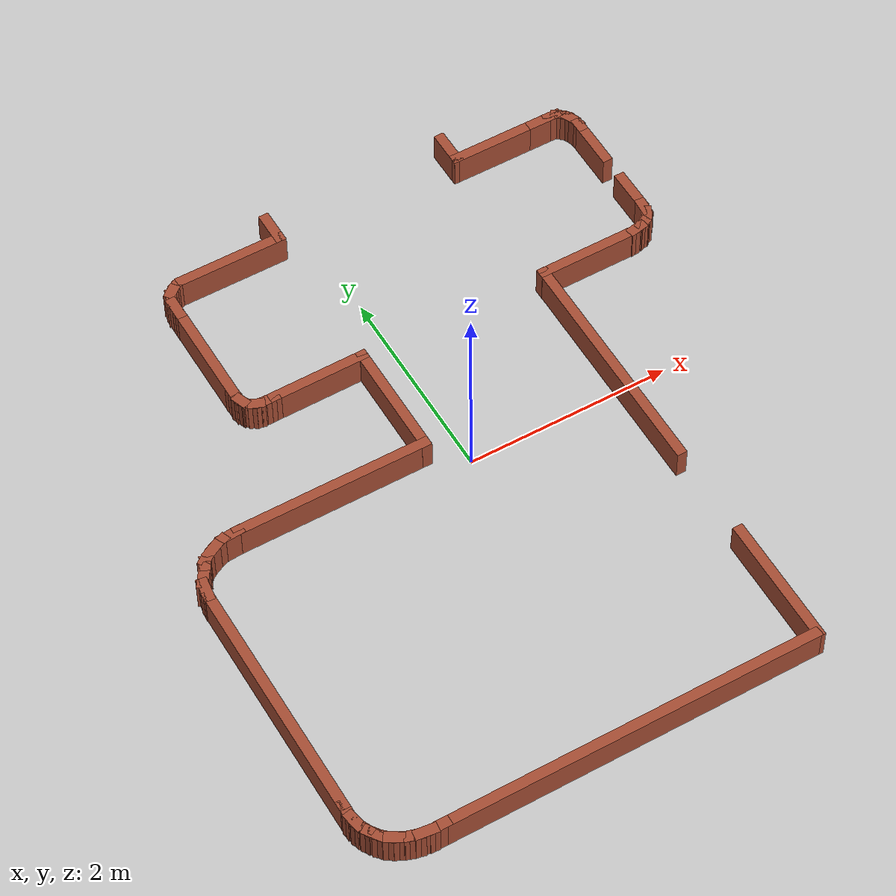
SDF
<?xml version='1.0'?>
<sdf version='1.6'>
  <model name='walls'>
    <link name='Wall_33'>
      <pose frame=''>-0.352583 3.02287 0 0 0 -1.5708</pose>
      <self_collide>0</self_collide>
      <enable_wind>0</enable_wind>
      <kinematic>0</kinematic>
      <visual name='Wall_33_Visual'>
        <pose frame=''>0 0 0.15 0 -0 0</pose>
        <geometry>
          <box>
            <size>0.357602 0.1 0.3</size>
          </box>
        </geometry>
        <material>
          <script>
            <uri>file://media/materials/scripts/gazebo.material</uri>
            <name>Gazebo/Bricks</name>
          </script>
          <ambient>1 1 1 1</ambient>
        </material>
        <meta>
          <layer>0</layer>
        </meta>
        <transparency>0</transparency>
        <cast_shadows>1</cast_shadows>
      </visual>
      <collision name='Wall_33_Collision'>
        <laser_retro>0</laser_retro>
        <max_contacts>10</max_contacts>
        <pose frame=''>0 0 0.15 0 -0 0</pose>
        <geometry>
          <box>
            <size>0.357602 0.1 0.3</size>
          </box>
        </geometry>
        <surface>
          <friction>
            <ode>
              <mu>1</mu>
              <mu2>1</mu2>
              <fdir1>0 0 0</fdir1>
              <slip1>0</slip1>
              <slip2>0</slip2>
            </ode>
            <torsional>
              <coefficient>1</coefficient>
              <patch_radius>0</patch_radius>
              <surface_radius>0</surface_radius>
              <use_patch_radius>1</use_patch_radius>
              <ode>
                <slip>0</slip>
              </ode>
            </torsional>
          </friction>
          <bounce>
            <restitution_coefficient>0</restitution_coefficient>
            <threshold>1e+06</threshold>
          </bounce>
          <contact>
            <collide_without_contact>0</collide_without_contact>
            <collide_without_contact_bitmask>1</collide_without_contact_bitmask>
            <collide_bitmask>1</collide_bitmask>
            <ode>
              <soft_cfm>0</soft_cfm>
              <soft_erp>0.2</soft_erp>
              <kp>1e+13</kp>
              <kd>1</kd>
              <max_vel>0.01</max_vel>
              <min_depth>0</min_depth>
            </ode>
            <bullet>
              <split_impulse>1</split_impulse>
              <split_impulse_penetration_threshold>-0.01</split_impulse_penetration_threshold>
              <soft_cfm>0</soft_cfm>
              <soft_erp>0.2</soft_erp>
              <kp>1e+13</kp>
              <kd>1</kd>
            </bullet>
          </contact>
        </surface>
      </collision>
    </link>
    <link name='Wall_34'>
      <pose frame=''>-0.854083 2.89387 0 0 -0 3.14159</pose>
      <self_collide>0</self_collide>
      <enable_wind>0</enable_wind>
      <kinematic>0</kinematic>
      <visual name='Wall_34_Visual'>
        <pose frame=''>0 0 0.15 0 -0 0</pose>
        <geometry>
          <box>
            <size>1.10348 0.1 0.3</size>
          </box>
        </geometry>
        <material>
          <script>
            <uri>file://media/materials/scripts/gazebo.material</uri>
            <name>Gazebo/Bricks</name>
          </script>
          <ambient>1 1 1 1</ambient>
        </material>
        <meta>
          <layer>0</layer>
        </meta>
        <transparency>0</transparency>
        <cast_shadows>1</cast_shadows>
      </visual>
      <collision name='Wall_34_Collision'>
        <laser_retro>0</laser_retro>
        <max_contacts>10</max_contacts>
        <pose frame=''>0 0 0.15 0 -0 0</pose>
        <geometry>
          <box>
            <size>1.10348 0.1 0.3</size>
          </box>
        </geometry>
        <surface>
          <friction>
            <ode>
              <mu>1</mu>
              <mu2>1</mu2>
              <fdir1>0 0 0</fdir1>
              <slip1>0</slip1>
              <slip2>0</slip2>
            </ode>
            <torsional>
              <coefficient>1</coefficient>
              <patch_radius>0</patch_radius>
              <surface_radius>0</surface_radius>
              <use_patch_radius>1</use_patch_radius>
              <ode>
                <slip>0</slip>
              </ode>
            </torsional>
          </friction>
          <bounce>
            <restitution_coefficient>0</restitution_coefficient>
            <threshold>1e+06</threshold>
          </bounce>
          <contact>
            <collide_without_contact>0</collide_without_contact>
            <collide_without_contact_bitmask>1</collide_without_contact_bitmask>
            <collide_bitmask>1</collide_bitmask>
            <ode>
              <soft_cfm>0</soft_cfm>
              <soft_erp>0.2</soft_erp>
              <kp>1e+13</kp>
              <kd>1</kd>
              <max_vel>0.01</max_vel>
              <min_depth>0</min_depth>
            </ode>
            <bullet>
              <split_impulse>1</split_impulse>
              <split_impulse_penetration_threshold>-0.01</split_impulse_penetration_threshold>
              <soft_cfm>0</soft_cfm>
              <soft_erp>0.2</soft_erp>
              <kp>1e+13</kp>
              <kd>1</kd>
            </bullet>
          </contact>
        </surface>
      </collision>
    </link>
    <link name='Wall_36'>
      <pose frame=''>-1.42108 2.87687 0 0 0 -2.69014</pose>
      <self_collide>0</self_collide>
      <enable_wind>0</enable_wind>
      <kinematic>0</kinematic>
      <visual name='Wall_36_Visual'>
        <pose frame=''>0 0 0.15 0 -0 0</pose>
        <geometry>
          <box>
            <size>0.136312 0.1 0.3</size>
          </box>
        </geometry>
        <material>
          <script>
            <uri>file://media/materials/scripts/gazebo.material</uri>
            <name>Gazebo/Bricks</name>
          </script>
          <ambient>1 1 1 1</ambient>
        </material>
        <meta>
          <layer>0</layer>
        </meta>
        <transparency>0</transparency>
        <cast_shadows>1</cast_shadows>
      </visual>
      <collision name='Wall_36_Collision'>
        <laser_retro>0</laser_retro>
        <max_contacts>10</max_contacts>
        <pose frame=''>0 0 0.15 0 -0 0</pose>
        <geometry>
          <box>
            <size>0.136312 0.1 0.3</size>
          </box>
        </geometry>
        <surface>
          <friction>
            <ode>
              <mu>1</mu>
              <mu2>1</mu2>
              <fdir1>0 0 0</fdir1>
              <slip1>0</slip1>
              <slip2>0</slip2>
            </ode>
            <torsional>
              <coefficient>1</coefficient>
              <patch_radius>0</patch_radius>
              <surface_radius>0</surface_radius>
              <use_patch_radius>1</use_patch_radius>
              <ode>
                <slip>0</slip>
              </ode>
            </torsional>
          </friction>
          <bounce>
            <restitution_coefficient>0</restitution_coefficient>
            <threshold>1e+06</threshold>
          </bounce>
          <contact>
            <collide_without_contact>0</collide_without_contact>
            <collide_without_contact_bitmask>1</collide_without_contact_bitmask>
            <collide_bitmask>1</collide_bitmask>
            <ode>
              <soft_cfm>0</soft_cfm>
              <soft_erp>0.2</soft_erp>
              <kp>1e+13</kp>
              <kd>1</kd>
              <max_vel>0.01</max_vel>
              <min_depth>0</min_depth>
            </ode>
            <bullet>
              <split_impulse>1</split_impulse>
              <split_impulse_penetration_threshold>-0.01</split_impulse_penetration_threshold>
              <soft_cfm>0</soft_cfm>
              <soft_erp>0.2</soft_erp>
              <kp>1e+13</kp>
              <kd>1</kd>
            </bullet>
          </contact>
        </surface>
      </collision>
    </link>
    <link name='Wall_37'>
      <pose frame=''>-1.45158 2.85937 0 0 0 -2.54539</pose>
      <self_collide>0</self_collide>
      <enable_wind>0</enable_wind>
      <kinematic>0</kinematic>
      <visual name='Wall_37_Visual'>
        <pose frame=''>0 0 0.15 0 -0 0</pose>
        <geometry>
          <box>
            <size>0.133838 0.1 0.3</size>
          </box>
        </geometry>
        <material>
          <script>
            <uri>file://media/materials/scripts/gazebo.material</uri>
            <name>Gazebo/Bricks</name>
          </script>
          <ambient>1 1 1 1</ambient>
        </material>
        <meta>
          <layer>0</layer>
        </meta>
        <transparency>0</transparency>
        <cast_shadows>1</cast_shadows>
      </visual>
      <collision name='Wall_37_Collision'>
        <laser_retro>0</laser_retro>
        <max_contacts>10</max_contacts>
        <pose frame=''>0 0 0.15 0 -0 0</pose>
        <geometry>
          <box>
            <size>0.133838 0.1 0.3</size>
          </box>
        </geometry>
        <surface>
          <friction>
            <ode>
              <mu>1</mu>
              <mu2>1</mu2>
              <fdir1>0 0 0</fdir1>
              <slip1>0</slip1>
              <slip2>0</slip2>
            </ode>
            <torsional>
              <coefficient>1</coefficient>
              <patch_radius>0</patch_radius>
              <surface_radius>0</surface_radius>
              <use_patch_radius>1</use_patch_radius>
              <ode>
                <slip>0</slip>
              </ode>
            </torsional>
          </friction>
          <bounce>
            <restitution_coefficient>0</restitution_coefficient>
            <threshold>1e+06</threshold>
          </bounce>
          <contact>
            <collide_without_contact>0</collide_without_contact>
            <collide_without_contact_bitmask>1</collide_without_contact_bitmask>
            <collide_bitmask>1</collide_bitmask>
            <ode>
              <soft_cfm>0</soft_cfm>
              <soft_erp>0.2</soft_erp>
              <kp>1e+13</kp>
              <kd>1</kd>
              <max_vel>0.01</max_vel>
              <min_depth>0</min_depth>
            </ode>
            <bullet>
              <split_impulse>1</split_impulse>
              <split_impulse_penetration_threshold>-0.01</split_impulse_penetration_threshold>
              <soft_cfm>0</soft_cfm>
              <soft_erp>0.2</soft_erp>
              <kp>1e+13</kp>
              <kd>1</kd>
            </bullet>
          </contact>
        </surface>
      </collision>
    </link>
    <link name='Wall_38'>
      <pose frame=''>-1.48958 2.83087 0 0 0 -2.47195</pose>
      <self_collide>0</self_collide>
      <enable_wind>0</enable_wind>
      <kinematic>0</kinematic>
      <visual name='Wall_38_Visual'>
        <pose frame=''>0 0 0.15 0 -0 0</pose>
        <geometry>
          <box>
            <size>0.161164 0.1 0.3</size>
          </box>
        </geometry>
        <material>
          <script>
            <uri>file://media/materials/scripts/gazebo.material</uri>
            <name>Gazebo/Bricks</name>
          </script>
          <ambient>1 1 1 1</ambient>
        </material>
        <meta>
          <layer>0</layer>
        </meta>
        <transparency>0</transparency>
        <cast_shadows>1</cast_shadows>
      </visual>
      <collision name='Wall_38_Collision'>
        <laser_retro>0</laser_retro>
        <max_contacts>10</max_contacts>
        <pose frame=''>0 0 0.15 0 -0 0</pose>
        <geometry>
          <box>
            <size>0.161164 0.1 0.3</size>
          </box>
        </geometry>
        <surface>
          <friction>
            <ode>
              <mu>1</mu>
              <mu2>1</mu2>
              <fdir1>0 0 0</fdir1>
              <slip1>0</slip1>
              <slip2>0</slip2>
            </ode>
            <torsional>
              <coefficient>1</coefficient>
              <patch_radius>0</patch_radius>
              <surface_radius>0</surface_radius>
              <use_patch_radius>1</use_patch_radius>
              <ode>
                <slip>0</slip>
              </ode>
            </torsional>
          </friction>
          <bounce>
            <restitution_coefficient>0</restitution_coefficient>
            <threshold>1e+06</threshold>
          </bounce>
          <contact>
            <collide_without_contact>0</collide_without_contact>
            <collide_without_contact_bitmask>1</collide_without_contact_bitmask>
            <collide_bitmask>1</collide_bitmask>
            <ode>
              <soft_cfm>0</soft_cfm>
              <soft_erp>0.2</soft_erp>
              <kp>1e+13</kp>
              <kd>1</kd>
              <max_vel>0.01</max_vel>
              <min_depth>0</min_depth>
            </ode>
            <bullet>
              <split_impulse>1</split_impulse>
              <split_impulse_penetration_threshold>-0.01</split_impulse_penetration_threshold>
              <soft_cfm>0</soft_cfm>
              <soft_erp>0.2</soft_erp>
              <kp>1e+13</kp>
              <kd>1</kd>
            </bullet>
          </contact>
        </surface>
      </collision>
    </link>
    <link name='Wall_39'>
      <pose frame=''>-1.52908 2.76337 0 0 0 -1.88013</pose>
      <self_collide>0</self_collide>
      <enable_wind>0</enable_wind>
      <kinematic>0</kinematic>
      <visual name='Wall_39_Visual'>
        <pose frame=''>0 0 0.15 0 -0 0</pose>
        <geometry>
          <box>
            <size>0.201833 0.1 0.3</size>
          </box>
        </geometry>
        <material>
          <script>
            <uri>file://media/materials/scripts/gazebo.material</uri>
            <name>Gazebo/Bricks</name>
          </script>
          <ambient>1 1 1 1</ambient>
        </material>
        <meta>
          <layer>0</layer>
        </meta>
        <transparency>0</transparency>
        <cast_shadows>1</cast_shadows>
      </visual>
      <collision name='Wall_39_Collision'>
        <laser_retro>0</laser_retro>
        <max_contacts>10</max_contacts>
        <pose frame=''>0 0 0.15 0 -0 0</pose>
        <geometry>
          <box>
            <size>0.201833 0.1 0.3</size>
          </box>
        </geometry>
        <surface>
          <friction>
            <ode>
              <mu>1</mu>
              <mu2>1</mu2>
              <fdir1>0 0 0</fdir1>
              <slip1>0</slip1>
              <slip2>0</slip2>
            </ode>
            <torsional>
              <coefficient>1</coefficient>
              <patch_radius>0</patch_radius>
              <surface_radius>0</surface_radius>
              <use_patch_radius>1</use_patch_radius>
              <ode>
                <slip>0</slip>
              </ode>
            </torsional>
          </friction>
          <bounce>
            <restitution_coefficient>0</restitution_coefficient>
            <threshold>1e+06</threshold>
          </bounce>
          <contact>
            <collide_without_contact>0</collide_without_contact>
            <collide_without_contact_bitmask>1</collide_without_contact_bitmask>
            <collide_bitmask>1</collide_bitmask>
            <ode>
              <soft_cfm>0</soft_cfm>
              <soft_erp>0.2</soft_erp>
              <kp>1e+13</kp>
              <kd>1</kd>
              <max_vel>0.01</max_vel>
              <min_depth>0</min_depth>
            </ode>
            <bullet>
              <split_impulse>1</split_impulse>
              <split_impulse_penetration_threshold>-0.01</split_impulse_penetration_threshold>
              <soft_cfm>0</soft_cfm>
              <soft_erp>0.2</soft_erp>
              <kp>1e+13</kp>
              <kd>1</kd>
            </bullet>
          </contact>
        </surface>
      </collision>
    </link>
    <link name='Wall_40'>
      <pose frame=''>-1.54458 2.63987 0 0 0 -1.5708</pose>
      <self_collide>0</self_collide>
      <enable_wind>0</enable_wind>
      <kinematic>0</kinematic>
      <visual name='Wall_40_Visual'>
        <pose frame=''>0 0 0.15 0 -0 0</pose>
        <geometry>
          <box>
            <size>0.25 0.1 0.3</size>
          </box>
        </geometry>
        <material>
          <script>
            <uri>file://media/materials/scripts/gazebo.material</uri>
            <name>Gazebo/Bricks</name>
          </script>
          <ambient>1 1 1 1</ambient>
        </material>
        <meta>
          <layer>0</layer>
        </meta>
        <transparency>0</transparency>
        <cast_shadows>1</cast_shadows>
      </visual>
      <collision name='Wall_40_Collision'>
        <laser_retro>0</laser_retro>
        <max_contacts>10</max_contacts>
        <pose frame=''>0 0 0.15 0 -0 0</pose>
        <geometry>
          <box>
            <size>0.25 0.1 0.3</size>
          </box>
        </geometry>
        <surface>
          <friction>
            <ode>
              <mu>1</mu>
              <mu2>1</mu2>
              <fdir1>0 0 0</fdir1>
              <slip1>0</slip1>
              <slip2>0</slip2>
            </ode>
            <torsional>
              <coefficient>1</coefficient>
              <patch_radius>0</patch_radius>
              <surface_radius>0</surface_radius>
              <use_patch_radius>1</use_patch_radius>
              <ode>
                <slip>0</slip>
              </ode>
            </torsional>
          </friction>
          <bounce>
            <restitution_coefficient>0</restitution_coefficient>
            <threshold>1e+06</threshold>
          </bounce>
          <contact>
            <collide_without_contact>0</collide_without_contact>
            <collide_without_contact_bitmask>1</collide_without_contact_bitmask>
            <collide_bitmask>1</collide_bitmask>
            <ode>
              <soft_cfm>0</soft_cfm>
              <soft_erp>0.2</soft_erp>
              <kp>1e+13</kp>
              <kd>1</kd>
              <max_vel>0.01</max_vel>
              <min_depth>0</min_depth>
            </ode>
            <bullet>
              <split_impulse>1</split_impulse>
              <split_impulse_penetration_threshold>-0.01</split_impulse_penetration_threshold>
              <soft_cfm>0</soft_cfm>
              <soft_erp>0.2</soft_erp>
              <kp>1e+13</kp>
              <kd>1</kd>
            </bullet>
          </contact>
        </surface>
      </collision>
    </link>
    <link name='Wall_41'>
      <pose frame=''>-1.54358 2.06137 0 0 0 -1.56881</pose>
      <self_collide>0</self_collide>
      <enable_wind>0</enable_wind>
      <kinematic>0</kinematic>
      <visual name='Wall_41_Visual'>
        <pose frame=''>0 0 0.15 0 -0 0</pose>
        <geometry>
          <box>
            <size>1.107 0.1 0.3</size>
          </box>
        </geometry>
        <material>
          <script>
            <uri>file://media/materials/scripts/gazebo.material</uri>
            <name>Gazebo/Bricks</name>
          </script>
          <ambient>1 1 1 1</ambient>
        </material>
        <meta>
          <layer>0</layer>
        </meta>
        <transparency>0</transparency>
        <cast_shadows>1</cast_shadows>
      </visual>
      <collision name='Wall_41_Collision'>
        <laser_retro>0</laser_retro>
        <max_contacts>10</max_contacts>
        <pose frame=''>0 0 0.15 0 -0 0</pose>
        <geometry>
          <box>
            <size>1.107 0.1 0.3</size>
          </box>
        </geometry>
        <surface>
          <friction>
            <ode>
              <mu>1</mu>
              <mu2>1</mu2>
              <fdir1>0 0 0</fdir1>
              <slip1>0</slip1>
              <slip2>0</slip2>
            </ode>
            <torsional>
              <coefficient>1</coefficient>
              <patch_radius>0</patch_radius>
              <surface_radius>0</surface_radius>
              <use_patch_radius>1</use_patch_radius>
              <ode>
                <slip>0</slip>
              </ode>
            </torsional>
          </friction>
          <bounce>
            <restitution_coefficient>0</restitution_coefficient>
            <threshold>1e+06</threshold>
          </bounce>
          <contact>
            <collide_without_contact>0</collide_without_contact>
            <collide_without_contact_bitmask>1</collide_without_contact_bitmask>
            <collide_bitmask>1</collide_bitmask>
            <ode>
              <soft_cfm>0</soft_cfm>
              <soft_erp>0.2</soft_erp>
              <kp>1e+13</kp>
              <kd>1</kd>
              <max_vel>0.01</max_vel>
              <min_depth>0</min_depth>
            </ode>
            <bullet>
              <split_impulse>1</split_impulse>
              <split_impulse_penetration_threshold>-0.01</split_impulse_penetration_threshold>
              <soft_cfm>0</soft_cfm>
              <soft_erp>0.2</soft_erp>
              <kp>1e+13</kp>
              <kd>1</kd>
            </bullet>
          </contact>
        </surface>
      </collision>
    </link>
    <link name='Wall_42'>
      <pose frame=''>-1.53958 1.50687 0 0 0 -1.51204</pose>
      <self_collide>0</self_collide>
      <enable_wind>0</enable_wind>
      <kinematic>0</kinematic>
      <visual name='Wall_42_Visual'>
        <pose frame=''>0 0 0.15 0 -0 0</pose>
        <geometry>
          <box>
            <size>0.2018 0.1 0.3</size>
          </box>
        </geometry>
        <material>
          <script>
            <uri>file://media/materials/scripts/gazebo.material</uri>
            <name>Gazebo/Bricks</name>
          </script>
          <ambient>1 1 1 1</ambient>
        </material>
        <meta>
          <layer>0</layer>
        </meta>
        <transparency>0</transparency>
        <cast_shadows>1</cast_shadows>
      </visual>
      <collision name='Wall_42_Collision'>
        <laser_retro>0</laser_retro>
        <max_contacts>10</max_contacts>
        <pose frame=''>0 0 0.15 0 -0 0</pose>
        <geometry>
          <box>
            <size>0.2018 0.1 0.3</size>
          </box>
        </geometry>
        <surface>
          <friction>
            <ode>
              <mu>1</mu>
              <mu2>1</mu2>
              <fdir1>0 0 0</fdir1>
              <slip1>0</slip1>
              <slip2>0</slip2>
            </ode>
            <torsional>
              <coefficient>1</coefficient>
              <patch_radius>0</patch_radius>
              <surface_radius>0</surface_radius>
              <use_patch_radius>1</use_patch_radius>
              <ode>
                <slip>0</slip>
              </ode>
            </torsional>
          </friction>
          <bounce>
            <restitution_coefficient>0</restitution_coefficient>
            <threshold>1e+06</threshold>
          </bounce>
          <contact>
            <collide_without_contact>0</collide_without_contact>
            <collide_without_contact_bitmask>1</collide_without_contact_bitmask>
            <collide_bitmask>1</collide_bitmask>
            <ode>
              <soft_cfm>0</soft_cfm>
              <soft_erp>0.2</soft_erp>
              <kp>1e+13</kp>
              <kd>1</kd>
              <max_vel>0.01</max_vel>
              <min_depth>0</min_depth>
            </ode>
            <bullet>
              <split_impulse>1</split_impulse>
              <split_impulse_penetration_threshold>-0.01</split_impulse_penetration_threshold>
              <soft_cfm>0</soft_cfm>
              <soft_erp>0.2</soft_erp>
              <kp>1e+13</kp>
              <kd>1</kd>
            </bullet>
          </contact>
        </surface>
      </collision>
    </link>
    <link name='Wall_43'>
      <pose frame=''>-1.52658 1.42887 0 0 0 -1.21609</pose>
      <self_collide>0</self_collide>
      <enable_wind>0</enable_wind>
      <kinematic>0</kinematic>
      <visual name='Wall_43_Visual'>
        <pose frame=''>0 0 0.15 0 -0 0</pose>
        <geometry>
          <box>
            <size>0.157996 0.1 0.3</size>
          </box>
        </geometry>
        <material>
          <script>
            <uri>file://media/materials/scripts/gazebo.material</uri>
            <name>Gazebo/Bricks</name>
          </script>
          <ambient>1 1 1 1</ambient>
        </material>
        <meta>
          <layer>0</layer>
        </meta>
        <transparency>0</transparency>
        <cast_shadows>1</cast_shadows>
      </visual>
      <collision name='Wall_43_Collision'>
        <laser_retro>0</laser_retro>
        <max_contacts>10</max_contacts>
        <pose frame=''>0 0 0.15 0 -0 0</pose>
        <geometry>
          <box>
            <size>0.157996 0.1 0.3</size>
          </box>
        </geometry>
        <surface>
          <friction>
            <ode>
              <mu>1</mu>
              <mu2>1</mu2>
              <fdir1>0 0 0</fdir1>
              <slip1>0</slip1>
              <slip2>0</slip2>
            </ode>
            <torsional>
              <coefficient>1</coefficient>
              <patch_radius>0</patch_radius>
              <surface_radius>0</surface_radius>
              <use_patch_radius>1</use_patch_radius>
              <ode>
                <slip>0</slip>
              </ode>
            </torsional>
          </friction>
          <bounce>
            <restitution_coefficient>0</restitution_coefficient>
            <threshold>1e+06</threshold>
          </bounce>
          <contact>
            <collide_without_contact>0</collide_without_contact>
            <collide_without_contact_bitmask>1</collide_without_contact_bitmask>
            <collide_bitmask>1</collide_bitmask>
            <ode>
              <soft_cfm>0</soft_cfm>
              <soft_erp>0.2</soft_erp>
              <kp>1e+13</kp>
              <kd>1</kd>
              <max_vel>0.01</max_vel>
              <min_depth>0</min_depth>
            </ode>
            <bullet>
              <split_impulse>1</split_impulse>
              <split_impulse_penetration_threshold>-0.01</split_impulse_penetration_threshold>
              <soft_cfm>0</soft_cfm>
              <soft_erp>0.2</soft_erp>
              <kp>1e+13</kp>
              <kd>1</kd>
            </bullet>
          </contact>
        </surface>
      </collision>
    </link>
    <link name='Wall_45'>
      <pose frame=''>-1.47208 1.35537 0 0 0 -0.678662</pose>
      <self_collide>0</self_collide>
      <enable_wind>0</enable_wind>
      <kinematic>0</kinematic>
      <visual name='Wall_45_Visual'>
        <pose frame=''>0 0 0.15 0 -0 0</pose>
        <geometry>
          <box>
            <size>0.140426 0.1 0.3</size>
          </box>
        </geometry>
        <material>
          <script>
            <uri>file://media/materials/scripts/gazebo.material</uri>
            <name>Gazebo/Bricks</name>
          </script>
          <ambient>1 1 1 1</ambient>
        </material>
        <meta>
          <layer>0</layer>
        </meta>
        <transparency>0</transparency>
        <cast_shadows>1</cast_shadows>
      </visual>
      <collision name='Wall_45_Collision'>
        <laser_retro>0</laser_retro>
        <max_contacts>10</max_contacts>
        <pose frame=''>0 0 0.15 0 -0 0</pose>
        <geometry>
          <box>
            <size>0.140426 0.1 0.3</size>
          </box>
        </geometry>
        <surface>
          <friction>
            <ode>
              <mu>1</mu>
              <mu2>1</mu2>
              <fdir1>0 0 0</fdir1>
              <slip1>0</slip1>
              <slip2>0</slip2>
            </ode>
            <torsional>
              <coefficient>1</coefficient>
              <patch_radius>0</patch_radius>
              <surface_radius>0</surface_radius>
              <use_patch_radius>1</use_patch_radius>
              <ode>
                <slip>0</slip>
              </ode>
            </torsional>
          </friction>
          <bounce>
            <restitution_coefficient>0</restitution_coefficient>
            <threshold>1e+06</threshold>
          </bounce>
          <contact>
            <collide_without_contact>0</collide_without_contact>
            <collide_without_contact_bitmask>1</collide_without_contact_bitmask>
            <collide_bitmask>1</collide_bitmask>
            <ode>
              <soft_cfm>0</soft_cfm>
              <soft_erp>0.2</soft_erp>
              <kp>1e+13</kp>
              <kd>1</kd>
              <max_vel>0.01</max_vel>
              <min_depth>0</min_depth>
            </ode>
            <bullet>
              <split_impulse>1</split_impulse>
              <split_impulse_penetration_threshold>-0.01</split_impulse_penetration_threshold>
              <soft_cfm>0</soft_cfm>
              <soft_erp>0.2</soft_erp>
              <kp>1e+13</kp>
              <kd>1</kd>
            </bullet>
          </contact>
        </surface>
      </collision>
    </link>
    <link name='Wall_46'>
      <pose frame=''>-1.42708 1.33137 0 0 0 -0.371709</pose>
      <self_collide>0</self_collide>
      <enable_wind>0</enable_wind>
      <kinematic>0</kinematic>
      <visual name='Wall_46_Visual'>
        <pose frame=''>0 0 0.15 0 -0 0</pose>
        <geometry>
          <box>
            <size>0.162952 0.1 0.3</size>
          </box>
        </geometry>
        <material>
          <script>
            <uri>file://media/materials/scripts/gazebo.material</uri>
            <name>Gazebo/Bricks</name>
          </script>
          <ambient>1 1 1 1</ambient>
        </material>
        <meta>
          <layer>0</layer>
        </meta>
        <transparency>0</transparency>
        <cast_shadows>1</cast_shadows>
      </visual>
      <collision name='Wall_46_Collision'>
        <laser_retro>0</laser_retro>
        <max_contacts>10</max_contacts>
        <pose frame=''>0 0 0.15 0 -0 0</pose>
        <geometry>
          <box>
            <size>0.162952 0.1 0.3</size>
          </box>
        </geometry>
        <surface>
          <friction>
            <ode>
              <mu>1</mu>
              <mu2>1</mu2>
              <fdir1>0 0 0</fdir1>
              <slip1>0</slip1>
              <slip2>0</slip2>
            </ode>
            <torsional>
              <coefficient>1</coefficient>
              <patch_radius>0</patch_radius>
              <surface_radius>0</surface_radius>
              <use_patch_radius>1</use_patch_radius>
              <ode>
                <slip>0</slip>
              </ode>
            </torsional>
          </friction>
          <bounce>
            <restitution_coefficient>0</restitution_coefficient>
            <threshold>1e+06</threshold>
          </bounce>
          <contact>
            <collide_without_contact>0</collide_without_contact>
            <collide_without_contact_bitmask>1</collide_without_contact_bitmask>
            <collide_bitmask>1</collide_bitmask>
            <ode>
              <soft_cfm>0</soft_cfm>
              <soft_erp>0.2</soft_erp>
              <kp>1e+13</kp>
              <kd>1</kd>
              <max_vel>0.01</max_vel>
              <min_depth>0</min_depth>
            </ode>
            <bullet>
              <split_impulse>1</split_impulse>
              <split_impulse_penetration_threshold>-0.01</split_impulse_penetration_threshold>
              <soft_cfm>0</soft_cfm>
              <soft_erp>0.2</soft_erp>
              <kp>1e+13</kp>
              <kd>1</kd>
            </bullet>
          </contact>
        </surface>
      </collision>
    </link>
    <link name='Wall_47'>
      <pose frame=''>-1.37458 1.31837 0 0 0 -0.065125</pose>
      <self_collide>0</self_collide>
      <enable_wind>0</enable_wind>
      <kinematic>0</kinematic>
      <visual name='Wall_47_Visual'>
        <pose frame=''>0 0 0.15 0 -0 0</pose>
        <geometry>
          <box>
            <size>0.146328 0.1 0.3</size>
          </box>
        </geometry>
        <material>
          <script>
            <uri>file://media/materials/scripts/gazebo.material</uri>
            <name>Gazebo/Bricks</name>
          </script>
          <ambient>1 1 1 1</ambient>
        </material>
        <meta>
          <layer>0</layer>
        </meta>
        <transparency>0</transparency>
        <cast_shadows>1</cast_shadows>
      </visual>
      <collision name='Wall_47_Collision'>
        <laser_retro>0</laser_retro>
        <max_contacts>10</max_contacts>
        <pose frame=''>0 0 0.15 0 -0 0</pose>
        <geometry>
          <box>
            <size>0.146328 0.1 0.3</size>
          </box>
        </geometry>
        <surface>
          <friction>
            <ode>
              <mu>1</mu>
              <mu2>1</mu2>
              <fdir1>0 0 0</fdir1>
              <slip1>0</slip1>
              <slip2>0</slip2>
            </ode>
            <torsional>
              <coefficient>1</coefficient>
              <patch_radius>0</patch_radius>
              <surface_radius>0</surface_radius>
              <use_patch_radius>1</use_patch_radius>
              <ode>
                <slip>0</slip>
              </ode>
            </torsional>
          </friction>
          <bounce>
            <restitution_coefficient>0</restitution_coefficient>
            <threshold>1e+06</threshold>
          </bounce>
          <contact>
            <collide_without_contact>0</collide_without_contact>
            <collide_without_contact_bitmask>1</collide_without_contact_bitmask>
            <collide_bitmask>1</collide_bitmask>
            <ode>
              <soft_cfm>0</soft_cfm>
              <soft_erp>0.2</soft_erp>
              <kp>1e+13</kp>
              <kd>1</kd>
              <max_vel>0.01</max_vel>
              <min_depth>0</min_depth>
            </ode>
            <bullet>
              <split_impulse>1</split_impulse>
              <split_impulse_penetration_threshold>-0.01</split_impulse_penetration_threshold>
              <soft_cfm>0</soft_cfm>
              <soft_erp>0.2</soft_erp>
              <kp>1e+13</kp>
              <kd>1</kd>
            </bullet>
          </contact>
        </surface>
      </collision>
    </link>
    <link name='Wall_48'>
      <pose frame=''>-1.30358 1.31687 0 0 -0 0</pose>
      <self_collide>0</self_collide>
      <enable_wind>0</enable_wind>
      <kinematic>0</kinematic>
      <visual name='Wall_48_Visual'>
        <pose frame=''>0 0 0.15 0 -0 0</pose>
        <geometry>
          <box>
            <size>0.19613 0.1 0.3</size>
          </box>
        </geometry>
        <material>
          <script>
            <uri>file://media/materials/scripts/gazebo.material</uri>
            <name>Gazebo/Bricks</name>
          </script>
          <ambient>1 1 1 1</ambient>
        </material>
        <meta>
          <layer>0</layer>
        </meta>
        <transparency>0</transparency>
        <cast_shadows>1</cast_shadows>
      </visual>
      <collision name='Wall_48_Collision'>
        <laser_retro>0</laser_retro>
        <max_contacts>10</max_contacts>
        <pose frame=''>0 0 0.15 0 -0 0</pose>
        <geometry>
          <box>
            <size>0.19613 0.1 0.3</size>
          </box>
        </geometry>
        <surface>
          <friction>
            <ode>
              <mu>1</mu>
              <mu2>1</mu2>
              <fdir1>0 0 0</fdir1>
              <slip1>0</slip1>
              <slip2>0</slip2>
            </ode>
            <torsional>
              <coefficient>1</coefficient>
              <patch_radius>0</patch_radius>
              <surface_radius>0</surface_radius>
              <use_patch_radius>1</use_patch_radius>
              <ode>
                <slip>0</slip>
              </ode>
            </torsional>
          </friction>
          <bounce>
            <restitution_coefficient>0</restitution_coefficient>
            <threshold>1e+06</threshold>
          </bounce>
          <contact>
            <collide_without_contact>0</collide_without_contact>
            <collide_without_contact_bitmask>1</collide_without_contact_bitmask>
            <collide_bitmask>1</collide_bitmask>
            <ode>
              <soft_cfm>0</soft_cfm>
              <soft_erp>0.2</soft_erp>
              <kp>1e+13</kp>
              <kd>1</kd>
              <max_vel>0.01</max_vel>
              <min_depth>0</min_depth>
            </ode>
            <bullet>
              <split_impulse>1</split_impulse>
              <split_impulse_penetration_threshold>-0.01</split_impulse_penetration_threshold>
              <soft_cfm>0</soft_cfm>
              <soft_erp>0.2</soft_erp>
              <kp>1e+13</kp>
              <kd>1</kd>
            </bullet>
          </contact>
        </surface>
      </collision>
    </link>
    <link name='Wall_49'>
      <pose frame=''>-0.805083 1.32087 0 0 -0 0.008879</pose>
      <self_collide>0</self_collide>
      <enable_wind>0</enable_wind>
      <kinematic>0</kinematic>
      <visual name='Wall_49_Visual'>
        <pose frame=''>0 0 0.15 0 -0 0</pose>
        <geometry>
          <box>
            <size>1.00152 0.1 0.3</size>
          </box>
        </geometry>
        <material>
          <script>
            <uri>file://media/materials/scripts/gazebo.material</uri>
            <name>Gazebo/Bricks</name>
          </script>
          <ambient>1 1 1 1</ambient>
        </material>
        <meta>
          <layer>0</layer>
        </meta>
        <transparency>0</transparency>
        <cast_shadows>1</cast_shadows>
      </visual>
      <collision name='Wall_49_Collision'>
        <laser_retro>0</laser_retro>
        <max_contacts>10</max_contacts>
        <pose frame=''>0 0 0.15 0 -0 0</pose>
        <geometry>
          <box>
            <size>1.00152 0.1 0.3</size>
          </box>
        </geometry>
        <surface>
          <friction>
            <ode>
              <mu>1</mu>
              <mu2>1</mu2>
              <fdir1>0 0 0</fdir1>
              <slip1>0</slip1>
              <slip2>0</slip2>
            </ode>
            <torsional>
              <coefficient>1</coefficient>
              <patch_radius>0</patch_radius>
              <surface_radius>0</surface_radius>
              <use_patch_radius>1</use_patch_radius>
              <ode>
                <slip>0</slip>
              </ode>
            </torsional>
          </friction>
          <bounce>
            <restitution_coefficient>0</restitution_coefficient>
            <threshold>1e+06</threshold>
          </bounce>
          <contact>
            <collide_without_contact>0</collide_without_contact>
            <collide_without_contact_bitmask>1</collide_without_contact_bitmask>
            <collide_bitmask>1</collide_bitmask>
            <ode>
              <soft_cfm>0</soft_cfm>
              <soft_erp>0.2</soft_erp>
              <kp>1e+13</kp>
              <kd>1</kd>
              <max_vel>0.01</max_vel>
              <min_depth>0</min_depth>
            </ode>
            <bullet>
              <split_impulse>1</split_impulse>
              <split_impulse_penetration_threshold>-0.01</split_impulse_penetration_threshold>
              <soft_cfm>0</soft_cfm>
              <soft_erp>0.2</soft_erp>
              <kp>1e+13</kp>
              <kd>1</kd>
            </bullet>
          </contact>
        </surface>
      </collision>
    </link>
    <link name='Wall_50'>
      <pose frame=''>-0.354083 0.768873 0 0 0 -1.5699</pose>
      <self_collide>0</self_collide>
      <enable_wind>0</enable_wind>
      <kinematic>0</kinematic>
      <visual name='Wall_50_Visual'>
        <pose frame=''>0 0 0.15 0 -0 0</pose>
        <geometry>
          <box>
            <size>1.21225 0.1 0.3</size>
          </box>
        </geometry>
        <material>
          <script>
            <uri>file://media/materials/scripts/gazebo.material</uri>
            <name>Gazebo/Bricks</name>
          </script>
          <ambient>1 1 1 1</ambient>
        </material>
        <meta>
          <layer>0</layer>
        </meta>
        <transparency>0</transparency>
        <cast_shadows>1</cast_shadows>
      </visual>
      <collision name='Wall_50_Collision'>
        <laser_retro>0</laser_retro>
        <max_contacts>10</max_contacts>
        <pose frame=''>0 0 0.15 0 -0 0</pose>
        <geometry>
          <box>
            <size>1.21225 0.1 0.3</size>
          </box>
        </geometry>
        <surface>
          <friction>
            <ode>
              <mu>1</mu>
              <mu2>1</mu2>
              <fdir1>0 0 0</fdir1>
              <slip1>0</slip1>
              <slip2>0</slip2>
            </ode>
            <torsional>
              <coefficient>1</coefficient>
              <patch_radius>0</patch_radius>
              <surface_radius>0</surface_radius>
              <use_patch_radius>1</use_patch_radius>
              <ode>
                <slip>0</slip>
              </ode>
            </torsional>
          </friction>
          <bounce>
            <restitution_coefficient>0</restitution_coefficient>
            <threshold>1e+06</threshold>
          </bounce>
          <contact>
            <collide_without_contact>0</collide_without_contact>
            <collide_without_contact_bitmask>1</collide_without_contact_bitmask>
            <collide_bitmask>1</collide_bitmask>
            <ode>
              <soft_cfm>0</soft_cfm>
              <soft_erp>0.2</soft_erp>
              <kp>1e+13</kp>
              <kd>1</kd>
              <max_vel>0.01</max_vel>
              <min_depth>0</min_depth>
            </ode>
            <bullet>
              <split_impulse>1</split_impulse>
              <split_impulse_penetration_threshold>-0.01</split_impulse_penetration_threshold>
              <soft_cfm>0</soft_cfm>
              <soft_erp>0.2</soft_erp>
              <kp>1e+13</kp>
              <kd>1</kd>
            </bullet>
          </contact>
        </surface>
      </collision>
    </link>
    <link name='Wall_51'>
      <pose frame=''>-1.27858 0.212873 0 0 -0 3.14159</pose>
      <self_collide>0</self_collide>
      <enable_wind>0</enable_wind>
      <kinematic>0</kinematic>
      <visual name='Wall_51_Visual'>
        <pose frame=''>0 0 0.15 0 -0 0</pose>
        <geometry>
          <box>
            <size>1.94962 0.1 0.3</size>
          </box>
        </geometry>
        <material>
          <script>
            <uri>file://media/materials/scripts/gazebo.material</uri>
            <name>Gazebo/Bricks</name>
          </script>
          <ambient>1 1 1 1</ambient>
        </material>
        <meta>
          <layer>0</layer>
        </meta>
        <transparency>0</transparency>
        <cast_shadows>1</cast_shadows>
      </visual>
      <collision name='Wall_51_Collision'>
        <laser_retro>0</laser_retro>
        <max_contacts>10</max_contacts>
        <pose frame=''>0 0 0.15 0 -0 0</pose>
        <geometry>
          <box>
            <size>1.94962 0.1 0.3</size>
          </box>
        </geometry>
        <surface>
          <friction>
            <ode>
              <mu>1</mu>
              <mu2>1</mu2>
              <fdir1>0 0 0</fdir1>
              <slip1>0</slip1>
              <slip2>0</slip2>
            </ode>
            <torsional>
              <coefficient>1</coefficient>
              <patch_radius>0</patch_radius>
              <surface_radius>0</surface_radius>
              <use_patch_radius>1</use_patch_radius>
              <ode>
                <slip>0</slip>
              </ode>
            </torsional>
          </friction>
          <bounce>
            <restitution_coefficient>0</restitution_coefficient>
            <threshold>1e+06</threshold>
          </bounce>
          <contact>
            <collide_without_contact>0</collide_without_contact>
            <collide_without_contact_bitmask>1</collide_without_contact_bitmask>
            <collide_bitmask>1</collide_bitmask>
            <ode>
              <soft_cfm>0</soft_cfm>
              <soft_erp>0.2</soft_erp>
              <kp>1e+13</kp>
              <kd>1</kd>
              <max_vel>0.01</max_vel>
              <min_depth>0</min_depth>
            </ode>
            <bullet>
              <split_impulse>1</split_impulse>
              <split_impulse_penetration_threshold>-0.01</split_impulse_penetration_threshold>
              <soft_cfm>0</soft_cfm>
              <soft_erp>0.2</soft_erp>
              <kp>1e+13</kp>
              <kd>1</kd>
            </bullet>
          </contact>
        </surface>
      </collision>
    </link>
    <link name='Wall_52'>
      <pose frame=''>-2.28158 0.207373 0 0 0 -3.0712</pose>
      <self_collide>0</self_collide>
      <enable_wind>0</enable_wind>
      <kinematic>0</kinematic>
      <visual name='Wall_52_Visual'>
        <pose frame=''>0 0 0.15 0 -0 0</pose>
        <geometry>
          <box>
            <size>0.256104 0.1 0.3</size>
          </box>
        </geometry>
        <material>
          <script>
            <uri>file://media/materials/scripts/gazebo.material</uri>
            <name>Gazebo/Bricks</name>
          </script>
          <ambient>1 1 1 1</ambient>
        </material>
        <meta>
          <layer>0</layer>
        </meta>
        <transparency>0</transparency>
        <cast_shadows>1</cast_shadows>
      </visual>
      <collision name='Wall_52_Collision'>
        <laser_retro>0</laser_retro>
        <max_contacts>10</max_contacts>
        <pose frame=''>0 0 0.15 0 -0 0</pose>
        <geometry>
          <box>
            <size>0.256104 0.1 0.3</size>
          </box>
        </geometry>
        <surface>
          <friction>
            <ode>
              <mu>1</mu>
              <mu2>1</mu2>
              <fdir1>0 0 0</fdir1>
              <slip1>0</slip1>
              <slip2>0</slip2>
            </ode>
            <torsional>
              <coefficient>1</coefficient>
              <patch_radius>0</patch_radius>
              <surface_radius>0</surface_radius>
              <use_patch_radius>1</use_patch_radius>
              <ode>
                <slip>0</slip>
              </ode>
            </torsional>
          </friction>
          <bounce>
            <restitution_coefficient>0</restitution_coefficient>
            <threshold>1e+06</threshold>
          </bounce>
          <contact>
            <collide_without_contact>0</collide_without_contact>
            <collide_without_contact_bitmask>1</collide_without_contact_bitmask>
            <collide_bitmask>1</collide_bitmask>
            <ode>
              <soft_cfm>0</soft_cfm>
              <soft_erp>0.2</soft_erp>
              <kp>1e+13</kp>
              <kd>1</kd>
              <max_vel>0.01</max_vel>
              <min_depth>0</min_depth>
            </ode>
            <bullet>
              <split_impulse>1</split_impulse>
              <split_impulse_penetration_threshold>-0.01</split_impulse_penetration_threshold>
              <soft_cfm>0</soft_cfm>
              <soft_erp>0.2</soft_erp>
              <kp>1e+13</kp>
              <kd>1</kd>
            </bullet>
          </contact>
        </surface>
      </collision>
    </link>
    <link name='Wall_53'>
      <pose frame=''>-2.39858 0.187373 0 0 0 -2.78564</pose>
      <self_collide>0</self_collide>
      <enable_wind>0</enable_wind>
      <kinematic>0</kinematic>
      <visual name='Wall_53_Visual'>
        <pose frame=''>0 0 0.15 0 -0 0</pose>
        <geometry>
          <box>
            <size>0.182791 0.1 0.3</size>
          </box>
        </geometry>
        <material>
          <script>
            <uri>file://media/materials/scripts/gazebo.material</uri>
            <name>Gazebo/Bricks</name>
          </script>
          <ambient>1 1 1 1</ambient>
        </material>
        <meta>
          <layer>0</layer>
        </meta>
        <transparency>0</transparency>
        <cast_shadows>1</cast_shadows>
      </visual>
      <collision name='Wall_53_Collision'>
        <laser_retro>0</laser_retro>
        <max_contacts>10</max_contacts>
        <pose frame=''>0 0 0.15 0 -0 0</pose>
        <geometry>
          <box>
            <size>0.182791 0.1 0.3</size>
          </box>
        </geometry>
        <surface>
          <friction>
            <ode>
              <mu>1</mu>
              <mu2>1</mu2>
              <fdir1>0 0 0</fdir1>
              <slip1>0</slip1>
              <slip2>0</slip2>
            </ode>
            <torsional>
              <coefficient>1</coefficient>
              <patch_radius>0</patch_radius>
              <surface_radius>0</surface_radius>
              <use_patch_radius>1</use_patch_radius>
              <ode>
                <slip>0</slip>
              </ode>
            </torsional>
          </friction>
          <bounce>
            <restitution_coefficient>0</restitution_coefficient>
            <threshold>1e+06</threshold>
          </bounce>
          <contact>
            <collide_without_contact>0</collide_without_contact>
            <collide_without_contact_bitmask>1</collide_without_contact_bitmask>
            <collide_bitmask>1</collide_bitmask>
            <ode>
              <soft_cfm>0</soft_cfm>
              <soft_erp>0.2</soft_erp>
              <kp>1e+13</kp>
              <kd>1</kd>
              <max_vel>0.01</max_vel>
              <min_depth>0</min_depth>
            </ode>
            <bullet>
              <split_impulse>1</split_impulse>
              <split_impulse_penetration_threshold>-0.01</split_impulse_penetration_threshold>
              <soft_cfm>0</soft_cfm>
              <soft_erp>0.2</soft_erp>
              <kp>1e+13</kp>
              <kd>1</kd>
            </bullet>
          </contact>
        </surface>
      </collision>
    </link>
    <link name='Wall_54'>
      <pose frame=''>-2.48458 0.148373 0 0 0 -2.66107</pose>
      <self_collide>0</self_collide>
      <enable_wind>0</enable_wind>
      <kinematic>0</kinematic>
      <visual name='Wall_54_Visual'>
        <pose frame=''>0 0 0.15 0 -0 0</pose>
        <geometry>
          <box>
            <size>0.205757 0.1 0.3</size>
          </box>
        </geometry>
        <material>
          <script>
            <uri>file://media/materials/scripts/gazebo.material</uri>
            <name>Gazebo/Bricks</name>
          </script>
          <ambient>1 1 1 1</ambient>
        </material>
        <meta>
          <layer>0</layer>
        </meta>
        <transparency>0</transparency>
        <cast_shadows>1</cast_shadows>
      </visual>
      <collision name='Wall_54_Collision'>
        <laser_retro>0</laser_retro>
        <max_contacts>10</max_contacts>
        <pose frame=''>0 0 0.15 0 -0 0</pose>
        <geometry>
          <box>
            <size>0.205757 0.1 0.3</size>
          </box>
        </geometry>
        <surface>
          <friction>
            <ode>
              <mu>1</mu>
              <mu2>1</mu2>
              <fdir1>0 0 0</fdir1>
              <slip1>0</slip1>
              <slip2>0</slip2>
            </ode>
            <torsional>
              <coefficient>1</coefficient>
              <patch_radius>0</patch_radius>
              <surface_radius>0</surface_radius>
              <use_patch_radius>1</use_patch_radius>
              <ode>
                <slip>0</slip>
              </ode>
            </torsional>
          </friction>
          <bounce>
            <restitution_coefficient>0</restitution_coefficient>
            <threshold>1e+06</threshold>
          </bounce>
          <contact>
            <collide_without_contact>0</collide_without_contact>
            <collide_without_contact_bitmask>1</collide_without_contact_bitmask>
            <collide_bitmask>1</collide_bitmask>
            <ode>
              <soft_cfm>0</soft_cfm>
              <soft_erp>0.2</soft_erp>
              <kp>1e+13</kp>
              <kd>1</kd>
              <max_vel>0.01</max_vel>
              <min_depth>0</min_depth>
            </ode>
            <bullet>
              <split_impulse>1</split_impulse>
              <split_impulse_penetration_threshold>-0.01</split_impulse_penetration_threshold>
              <soft_cfm>0</soft_cfm>
              <soft_erp>0.2</soft_erp>
              <kp>1e+13</kp>
              <kd>1</kd>
            </bullet>
          </contact>
        </surface>
      </collision>
    </link>
    <link name='Wall_55'>
      <pose frame=''>-2.56558 0.099873 0 0 0 -2.52693</pose>
      <self_collide>0</self_collide>
      <enable_wind>0</enable_wind>
      <kinematic>0</kinematic>
      <visual name='Wall_55_Visual'>
        <pose frame=''>0 0 0.15 0 -0 0</pose>
        <geometry>
          <box>
            <size>0.183298 0.1 0.3</size>
          </box>
        </geometry>
        <material>
          <script>
            <uri>file://media/materials/scripts/gazebo.material</uri>
            <name>Gazebo/Bricks</name>
          </script>
          <ambient>1 1 1 1</ambient>
        </material>
        <meta>
          <layer>0</layer>
        </meta>
        <transparency>0</transparency>
        <cast_shadows>1</cast_shadows>
      </visual>
      <collision name='Wall_55_Collision'>
        <laser_retro>0</laser_retro>
        <max_contacts>10</max_contacts>
        <pose frame=''>0 0 0.15 0 -0 0</pose>
        <geometry>
          <box>
            <size>0.183298 0.1 0.3</size>
          </box>
        </geometry>
        <surface>
          <friction>
            <ode>
              <mu>1</mu>
              <mu2>1</mu2>
              <fdir1>0 0 0</fdir1>
              <slip1>0</slip1>
              <slip2>0</slip2>
            </ode>
            <torsional>
              <coefficient>1</coefficient>
              <patch_radius>0</patch_radius>
              <surface_radius>0</surface_radius>
              <use_patch_radius>1</use_patch_radius>
              <ode>
                <slip>0</slip>
              </ode>
            </torsional>
          </friction>
          <bounce>
            <restitution_coefficient>0</restitution_coefficient>
            <threshold>1e+06</threshold>
          </bounce>
          <contact>
            <collide_without_contact>0</collide_without_contact>
            <collide_without_contact_bitmask>1</collide_without_contact_bitmask>
            <collide_bitmask>1</collide_bitmask>
            <ode>
              <soft_cfm>0</soft_cfm>
              <soft_erp>0.2</soft_erp>
              <kp>1e+13</kp>
              <kd>1</kd>
              <max_vel>0.01</max_vel>
              <min_depth>0</min_depth>
            </ode>
            <bullet>
              <split_impulse>1</split_impulse>
              <split_impulse_penetration_threshold>-0.01</split_impulse_penetration_threshold>
              <soft_cfm>0</soft_cfm>
              <soft_erp>0.2</soft_erp>
              <kp>1e+13</kp>
              <kd>1</kd>
            </bullet>
          </contact>
        </surface>
      </collision>
    </link>
    <link name='Wall_56'>
      <pose frame=''>-2.60933 0.053873 0 0 0 -1.98783</pose>
      <self_collide>0</self_collide>
      <enable_wind>0</enable_wind>
      <kinematic>0</kinematic>
      <visual name='Wall_56_Visual'>
        <pose frame=''>0 0 0.15 0 -0 0</pose>
        <geometry>
          <box>
            <size>0.149001 0.1 0.3</size>
          </box>
        </geometry>
        <material>
          <script>
            <uri>file://media/materials/scripts/gazebo.material</uri>
            <name>Gazebo/Bricks</name>
          </script>
          <ambient>1 1 1 1</ambient>
        </material>
        <meta>
          <layer>0</layer>
        </meta>
        <transparency>0</transparency>
        <cast_shadows>1</cast_shadows>
      </visual>
      <collision name='Wall_56_Collision'>
        <laser_retro>0</laser_retro>
        <max_contacts>10</max_contacts>
        <pose frame=''>0 0 0.15 0 -0 0</pose>
        <geometry>
          <box>
            <size>0.149001 0.1 0.3</size>
          </box>
        </geometry>
        <surface>
          <friction>
            <ode>
              <mu>1</mu>
              <mu2>1</mu2>
              <fdir1>0 0 0</fdir1>
              <slip1>0</slip1>
              <slip2>0</slip2>
            </ode>
            <torsional>
              <coefficient>1</coefficient>
              <patch_radius>0</patch_radius>
              <surface_radius>0</surface_radius>
              <use_patch_radius>1</use_patch_radius>
              <ode>
                <slip>0</slip>
              </ode>
            </torsional>
          </friction>
          <bounce>
            <restitution_coefficient>0</restitution_coefficient>
            <threshold>1e+06</threshold>
          </bounce>
          <contact>
            <collide_without_contact>0</collide_without_contact>
            <collide_without_contact_bitmask>1</collide_without_contact_bitmask>
            <collide_bitmask>1</collide_bitmask>
            <ode>
              <soft_cfm>0</soft_cfm>
              <soft_erp>0.2</soft_erp>
              <kp>1e+13</kp>
              <kd>1</kd>
              <max_vel>0.01</max_vel>
              <min_depth>0</min_depth>
            </ode>
            <bullet>
              <split_impulse>1</split_impulse>
              <split_impulse_penetration_threshold>-0.01</split_impulse_penetration_threshold>
              <soft_cfm>0</soft_cfm>
              <soft_erp>0.2</soft_erp>
              <kp>1e+13</kp>
              <kd>1</kd>
            </bullet>
          </contact>
        </surface>
      </collision>
    </link>
    <link name='Wall_57'>
      <pose frame=''>-2.67015 -0.041127 0 0 0 -2.16195</pose>
      <self_collide>0</self_collide>
      <enable_wind>0</enable_wind>
      <kinematic>0</kinematic>
      <visual name='Wall_57_Visual'>
        <pose frame=''>0 0 0.15 0 -0 0</pose>
        <geometry>
          <box>
            <size>0.275841 0.1 0.3</size>
          </box>
        </geometry>
        <material>
          <script>
            <uri>file://media/materials/scripts/gazebo.material</uri>
            <name>Gazebo/Bricks</name>
          </script>
          <ambient>1 1 1 1</ambient>
        </material>
        <meta>
          <layer>0</layer>
        </meta>
        <transparency>0</transparency>
        <cast_shadows>1</cast_shadows>
      </visual>
      <collision name='Wall_57_Collision'>
        <laser_retro>0</laser_retro>
        <max_contacts>10</max_contacts>
        <pose frame=''>0 0 0.15 0 -0 0</pose>
        <geometry>
          <box>
            <size>0.275841 0.1 0.3</size>
          </box>
        </geometry>
        <surface>
          <friction>
            <ode>
              <mu>1</mu>
              <mu2>1</mu2>
              <fdir1>0 0 0</fdir1>
              <slip1>0</slip1>
              <slip2>0</slip2>
            </ode>
            <torsional>
              <coefficient>1</coefficient>
              <patch_radius>0</patch_radius>
              <surface_radius>0</surface_radius>
              <use_patch_radius>1</use_patch_radius>
              <ode>
                <slip>0</slip>
              </ode>
            </torsional>
          </friction>
          <bounce>
            <restitution_coefficient>0</restitution_coefficient>
            <threshold>1e+06</threshold>
          </bounce>
          <contact>
            <collide_without_contact>0</collide_without_contact>
            <collide_without_contact_bitmask>1</collide_without_contact_bitmask>
            <collide_bitmask>1</collide_bitmask>
            <ode>
              <soft_cfm>0</soft_cfm>
              <soft_erp>0.2</soft_erp>
              <kp>1e+13</kp>
              <kd>1</kd>
              <max_vel>0.01</max_vel>
              <min_depth>0</min_depth>
            </ode>
            <bullet>
              <split_impulse>1</split_impulse>
              <split_impulse_penetration_threshold>-0.01</split_impulse_penetration_threshold>
              <soft_cfm>0</soft_cfm>
              <soft_erp>0.2</soft_erp>
              <kp>1e+13</kp>
              <kd>1</kd>
            </bullet>
          </contact>
        </surface>
      </collision>
    </link>
    <link name='Wall_58'>
      <pose frame=''>-2.72683 -0.185127 0 0 0 -1.70732</pose>
      <self_collide>0</self_collide>
      <enable_wind>0</enable_wind>
      <kinematic>0</kinematic>
      <visual name='Wall_58_Visual'>
        <pose frame=''>0 0 0.15 0 -0 0</pose>
        <geometry>
          <box>
            <size>0.243066 0.1 0.3</size>
          </box>
        </geometry>
        <material>
          <script>
            <uri>file://media/materials/scripts/gazebo.material</uri>
            <name>Gazebo/Bricks</name>
          </script>
          <ambient>1 1 1 1</ambient>
        </material>
        <meta>
          <layer>0</layer>
        </meta>
        <transparency>0</transparency>
        <cast_shadows>1</cast_shadows>
      </visual>
      <collision name='Wall_58_Collision'>
        <laser_retro>0</laser_retro>
        <max_contacts>10</max_contacts>
        <pose frame=''>0 0 0.15 0 -0 0</pose>
        <geometry>
          <box>
            <size>0.243066 0.1 0.3</size>
          </box>
        </geometry>
        <surface>
          <friction>
            <ode>
              <mu>1</mu>
              <mu2>1</mu2>
              <fdir1>0 0 0</fdir1>
              <slip1>0</slip1>
              <slip2>0</slip2>
            </ode>
            <torsional>
              <coefficient>1</coefficient>
              <patch_radius>0</patch_radius>
              <surface_radius>0</surface_radius>
              <use_patch_radius>1</use_patch_radius>
              <ode>
                <slip>0</slip>
              </ode>
            </torsional>
          </friction>
          <bounce>
            <restitution_coefficient>0</restitution_coefficient>
            <threshold>1e+06</threshold>
          </bounce>
          <contact>
            <collide_without_contact>0</collide_without_contact>
            <collide_without_contact_bitmask>1</collide_without_contact_bitmask>
            <collide_bitmask>1</collide_bitmask>
            <ode>
              <soft_cfm>0</soft_cfm>
              <soft_erp>0.2</soft_erp>
              <kp>1e+13</kp>
              <kd>1</kd>
              <max_vel>0.01</max_vel>
              <min_depth>0</min_depth>
            </ode>
            <bullet>
              <split_impulse>1</split_impulse>
              <split_impulse_penetration_threshold>-0.01</split_impulse_penetration_threshold>
              <soft_cfm>0</soft_cfm>
              <soft_erp>0.2</soft_erp>
              <kp>1e+13</kp>
              <kd>1</kd>
            </bullet>
          </contact>
        </surface>
      </collision>
    </link>
    <link name='Wall_59'>
      <pose frame=''>-2.73658 -1.43113 0 0 0 -1.5708</pose>
      <self_collide>0</self_collide>
      <enable_wind>0</enable_wind>
      <kinematic>0</kinematic>
      <visual name='Wall_59_Visual'>
        <pose frame=''>0 0 0.15 0 -0 0</pose>
        <geometry>
          <box>
            <size>2.44985 0.1 0.3</size>
          </box>
        </geometry>
        <material>
          <script>
            <uri>file://media/materials/scripts/gazebo.material</uri>
            <name>Gazebo/Bricks</name>
          </script>
          <ambient>1 1 1 1</ambient>
        </material>
        <meta>
          <layer>0</layer>
        </meta>
        <transparency>0</transparency>
        <cast_shadows>1</cast_shadows>
      </visual>
      <collision name='Wall_59_Collision'>
        <laser_retro>0</laser_retro>
        <max_contacts>10</max_contacts>
        <pose frame=''>0 0 0.15 0 -0 0</pose>
        <geometry>
          <box>
            <size>2.44985 0.1 0.3</size>
          </box>
        </geometry>
        <surface>
          <friction>
            <ode>
              <mu>1</mu>
              <mu2>1</mu2>
              <fdir1>0 0 0</fdir1>
              <slip1>0</slip1>
              <slip2>0</slip2>
            </ode>
            <torsional>
              <coefficient>1</coefficient>
              <patch_radius>0</patch_radius>
              <surface_radius>0</surface_radius>
              <use_patch_radius>1</use_patch_radius>
              <ode>
                <slip>0</slip>
              </ode>
            </torsional>
          </friction>
          <bounce>
            <restitution_coefficient>0</restitution_coefficient>
            <threshold>1e+06</threshold>
          </bounce>
          <contact>
            <collide_without_contact>0</collide_without_contact>
            <collide_without_contact_bitmask>1</collide_without_contact_bitmask>
            <collide_bitmask>1</collide_bitmask>
            <ode>
              <soft_cfm>0</soft_cfm>
              <soft_erp>0.2</soft_erp>
              <kp>1e+13</kp>
              <kd>1</kd>
              <max_vel>0.01</max_vel>
              <min_depth>0</min_depth>
            </ode>
            <bullet>
              <split_impulse>1</split_impulse>
              <split_impulse_penetration_threshold>-0.01</split_impulse_penetration_threshold>
              <soft_cfm>0</soft_cfm>
              <soft_erp>0.2</soft_erp>
              <kp>1e+13</kp>
              <kd>1</kd>
            </bullet>
          </contact>
        </surface>
      </collision>
    </link>
    <link name='Wall_60'>
      <pose frame=''>-2.73658 -2.66913 0 0 0 -1.5708</pose>
      <self_collide>0</self_collide>
      <enable_wind>0</enable_wind>
      <kinematic>0</kinematic>
      <visual name='Wall_60_Visual'>
        <pose frame=''>0 0 0.15 0 -0 0</pose>
        <geometry>
          <box>
            <size>0.226335 0.1 0.3</size>
          </box>
        </geometry>
        <material>
          <script>
            <uri>file://media/materials/scripts/gazebo.material</uri>
            <name>Gazebo/Bricks</name>
          </script>
          <ambient>1 1 1 1</ambient>
        </material>
        <meta>
          <layer>0</layer>
        </meta>
        <transparency>0</transparency>
        <cast_shadows>1</cast_shadows>
      </visual>
      <collision name='Wall_60_Collision'>
        <laser_retro>0</laser_retro>
        <max_contacts>10</max_contacts>
        <pose frame=''>0 0 0.15 0 -0 0</pose>
        <geometry>
          <box>
            <size>0.226335 0.1 0.3</size>
          </box>
        </geometry>
        <surface>
          <friction>
            <ode>
              <mu>1</mu>
              <mu2>1</mu2>
              <fdir1>0 0 0</fdir1>
              <slip1>0</slip1>
              <slip2>0</slip2>
            </ode>
            <torsional>
              <coefficient>1</coefficient>
              <patch_radius>0</patch_radius>
              <surface_radius>0</surface_radius>
              <use_patch_radius>1</use_patch_radius>
              <ode>
                <slip>0</slip>
              </ode>
            </torsional>
          </friction>
          <bounce>
            <restitution_coefficient>0</restitution_coefficient>
            <threshold>1e+06</threshold>
          </bounce>
          <contact>
            <collide_without_contact>0</collide_without_contact>
            <collide_without_contact_bitmask>1</collide_without_contact_bitmask>
            <collide_bitmask>1</collide_bitmask>
            <ode>
              <soft_cfm>0</soft_cfm>
              <soft_erp>0.2</soft_erp>
              <kp>1e+13</kp>
              <kd>1</kd>
              <max_vel>0.01</max_vel>
              <min_depth>0</min_depth>
            </ode>
            <bullet>
              <split_impulse>1</split_impulse>
              <split_impulse_penetration_threshold>-0.01</split_impulse_penetration_threshold>
              <soft_cfm>0</soft_cfm>
              <soft_erp>0.2</soft_erp>
              <kp>1e+13</kp>
              <kd>1</kd>
            </bullet>
          </contact>
        </surface>
      </collision>
    </link>
    <link name='Wall_61'>
      <pose frame=''>-2.72658 -2.78313 0 0 0 -1.37717</pose>
      <self_collide>0</self_collide>
      <enable_wind>0</enable_wind>
      <kinematic>0</kinematic>
      <visual name='Wall_61_Visual'>
        <pose frame=''>0 0 0.15 0 -0 0</pose>
        <geometry>
          <box>
            <size>0.203942 0.1 0.3</size>
          </box>
        </geometry>
        <material>
          <script>
            <uri>file://media/materials/scripts/gazebo.material</uri>
            <name>Gazebo/Bricks</name>
          </script>
          <ambient>1 1 1 1</ambient>
        </material>
        <meta>
          <layer>0</layer>
        </meta>
        <transparency>0</transparency>
        <cast_shadows>1</cast_shadows>
      </visual>
      <collision name='Wall_61_Collision'>
        <laser_retro>0</laser_retro>
        <max_contacts>10</max_contacts>
        <pose frame=''>0 0 0.15 0 -0 0</pose>
        <geometry>
          <box>
            <size>0.203942 0.1 0.3</size>
          </box>
        </geometry>
        <surface>
          <friction>
            <ode>
              <mu>1</mu>
              <mu2>1</mu2>
              <fdir1>0 0 0</fdir1>
              <slip1>0</slip1>
              <slip2>0</slip2>
            </ode>
            <torsional>
              <coefficient>1</coefficient>
              <patch_radius>0</patch_radius>
              <surface_radius>0</surface_radius>
              <use_patch_radius>1</use_patch_radius>
              <ode>
                <slip>0</slip>
              </ode>
            </torsional>
          </friction>
          <bounce>
            <restitution_coefficient>0</restitution_coefficient>
            <threshold>1e+06</threshold>
          </bounce>
          <contact>
            <collide_without_contact>0</collide_without_contact>
            <collide_without_contact_bitmask>1</collide_without_contact_bitmask>
            <collide_bitmask>1</collide_bitmask>
            <ode>
              <soft_cfm>0</soft_cfm>
              <soft_erp>0.2</soft_erp>
              <kp>1e+13</kp>
              <kd>1</kd>
              <max_vel>0.01</max_vel>
              <min_depth>0</min_depth>
            </ode>
            <bullet>
              <split_impulse>1</split_impulse>
              <split_impulse_penetration_threshold>-0.01</split_impulse_penetration_threshold>
              <soft_cfm>0</soft_cfm>
              <soft_erp>0.2</soft_erp>
              <kp>1e+13</kp>
              <kd>1</kd>
            </bullet>
          </contact>
        </surface>
      </collision>
    </link>
    <link name='Wall_62'>
      <pose frame=''>-2.69708 -2.87663 0 0 0 -1.14063</pose>
      <self_collide>0</self_collide>
      <enable_wind>0</enable_wind>
      <kinematic>0</kinematic>
      <visual name='Wall_62_Visual'>
        <pose frame=''>0 0 0.15 0 -0 0</pose>
        <geometry>
          <box>
            <size>0.193335 0.1 0.3</size>
          </box>
        </geometry>
        <material>
          <script>
            <uri>file://media/materials/scripts/gazebo.material</uri>
            <name>Gazebo/Bricks</name>
          </script>
          <ambient>1 1 1 1</ambient>
        </material>
        <meta>
          <layer>0</layer>
        </meta>
        <transparency>0</transparency>
        <cast_shadows>1</cast_shadows>
      </visual>
      <collision name='Wall_62_Collision'>
        <laser_retro>0</laser_retro>
        <max_contacts>10</max_contacts>
        <pose frame=''>0 0 0.15 0 -0 0</pose>
        <geometry>
          <box>
            <size>0.193335 0.1 0.3</size>
          </box>
        </geometry>
        <surface>
          <friction>
            <ode>
              <mu>1</mu>
              <mu2>1</mu2>
              <fdir1>0 0 0</fdir1>
              <slip1>0</slip1>
              <slip2>0</slip2>
            </ode>
            <torsional>
              <coefficient>1</coefficient>
              <patch_radius>0</patch_radius>
              <surface_radius>0</surface_radius>
              <use_patch_radius>1</use_patch_radius>
              <ode>
                <slip>0</slip>
              </ode>
            </torsional>
          </friction>
          <bounce>
            <restitution_coefficient>0</restitution_coefficient>
            <threshold>1e+06</threshold>
          </bounce>
          <contact>
            <collide_without_contact>0</collide_without_contact>
            <collide_without_contact_bitmask>1</collide_without_contact_bitmask>
            <collide_bitmask>1</collide_bitmask>
            <ode>
              <soft_cfm>0</soft_cfm>
              <soft_erp>0.2</soft_erp>
              <kp>1e+13</kp>
              <kd>1</kd>
              <max_vel>0.01</max_vel>
              <min_depth>0</min_depth>
            </ode>
            <bullet>
              <split_impulse>1</split_impulse>
              <split_impulse_penetration_threshold>-0.01</split_impulse_penetration_threshold>
              <soft_cfm>0</soft_cfm>
              <soft_erp>0.2</soft_erp>
              <kp>1e+13</kp>
              <kd>1</kd>
            </bullet>
          </contact>
        </surface>
      </collision>
    </link>
    <link name='Wall_63'>
      <pose frame=''>-2.64908 -2.95963 0 0 0 -0.957589</pose>
      <self_collide>0</self_collide>
      <enable_wind>0</enable_wind>
      <kinematic>0</kinematic>
      <visual name='Wall_63_Visual'>
        <pose frame=''>0 0 0.15 0 -0 0</pose>
        <geometry>
          <box>
            <size>0.19904 0.1 0.3</size>
          </box>
        </geometry>
        <material>
          <script>
            <uri>file://media/materials/scripts/gazebo.material</uri>
            <name>Gazebo/Bricks</name>
          </script>
          <ambient>1 1 1 1</ambient>
        </material>
        <meta>
          <layer>0</layer>
        </meta>
        <transparency>0</transparency>
        <cast_shadows>1</cast_shadows>
      </visual>
      <collision name='Wall_63_Collision'>
        <laser_retro>0</laser_retro>
        <max_contacts>10</max_contacts>
        <pose frame=''>0 0 0.15 0 -0 0</pose>
        <geometry>
          <box>
            <size>0.19904 0.1 0.3</size>
          </box>
        </geometry>
        <surface>
          <friction>
            <ode>
              <mu>1</mu>
              <mu2>1</mu2>
              <fdir1>0 0 0</fdir1>
              <slip1>0</slip1>
              <slip2>0</slip2>
            </ode>
            <torsional>
              <coefficient>1</coefficient>
              <patch_radius>0</patch_radius>
              <surface_radius>0</surface_radius>
              <use_patch_radius>1</use_patch_radius>
              <ode>
                <slip>0</slip>
              </ode>
            </torsional>
          </friction>
          <bounce>
            <restitution_coefficient>0</restitution_coefficient>
            <threshold>1e+06</threshold>
          </bounce>
          <contact>
            <collide_without_contact>0</collide_without_contact>
            <collide_without_contact_bitmask>1</collide_without_contact_bitmask>
            <collide_bitmask>1</collide_bitmask>
            <ode>
              <soft_cfm>0</soft_cfm>
              <soft_erp>0.2</soft_erp>
              <kp>1e+13</kp>
              <kd>1</kd>
              <max_vel>0.01</max_vel>
              <min_depth>0</min_depth>
            </ode>
            <bullet>
              <split_impulse>1</split_impulse>
              <split_impulse_penetration_threshold>-0.01</split_impulse_penetration_threshold>
              <soft_cfm>0</soft_cfm>
              <soft_erp>0.2</soft_erp>
              <kp>1e+13</kp>
              <kd>1</kd>
            </bullet>
          </contact>
        </surface>
      </collision>
    </link>
    <link name='Wall_64'>
      <pose frame=''>-2.59008 -3.02863 0 0 0 -0.751513</pose>
      <self_collide>0</self_collide>
      <enable_wind>0</enable_wind>
      <kinematic>0</kinematic>
      <visual name='Wall_64_Visual'>
        <pose frame=''>0 0 0.15 0 -0 0</pose>
        <geometry>
          <box>
            <size>0.182964 0.1 0.3</size>
          </box>
        </geometry>
        <material>
          <script>
            <uri>file://media/materials/scripts/gazebo.material</uri>
            <name>Gazebo/Bricks</name>
          </script>
          <ambient>1 1 1 1</ambient>
        </material>
        <meta>
          <layer>0</layer>
        </meta>
        <transparency>0</transparency>
        <cast_shadows>1</cast_shadows>
      </visual>
      <collision name='Wall_64_Collision'>
        <laser_retro>0</laser_retro>
        <max_contacts>10</max_contacts>
        <pose frame=''>0 0 0.15 0 -0 0</pose>
        <geometry>
          <box>
            <size>0.182964 0.1 0.3</size>
          </box>
        </geometry>
        <surface>
          <friction>
            <ode>
              <mu>1</mu>
              <mu2>1</mu2>
              <fdir1>0 0 0</fdir1>
              <slip1>0</slip1>
              <slip2>0</slip2>
            </ode>
            <torsional>
              <coefficient>1</coefficient>
              <patch_radius>0</patch_radius>
              <surface_radius>0</surface_radius>
              <use_patch_radius>1</use_patch_radius>
              <ode>
                <slip>0</slip>
              </ode>
            </torsional>
          </friction>
          <bounce>
            <restitution_coefficient>0</restitution_coefficient>
            <threshold>1e+06</threshold>
          </bounce>
          <contact>
            <collide_without_contact>0</collide_without_contact>
            <collide_without_contact_bitmask>1</collide_without_contact_bitmask>
            <collide_bitmask>1</collide_bitmask>
            <ode>
              <soft_cfm>0</soft_cfm>
              <soft_erp>0.2</soft_erp>
              <kp>1e+13</kp>
              <kd>1</kd>
              <max_vel>0.01</max_vel>
              <min_depth>0</min_depth>
            </ode>
            <bullet>
              <split_impulse>1</split_impulse>
              <split_impulse_penetration_threshold>-0.01</split_impulse_penetration_threshold>
              <soft_cfm>0</soft_cfm>
              <soft_erp>0.2</soft_erp>
              <kp>1e+13</kp>
              <kd>1</kd>
            </bullet>
          </contact>
        </surface>
      </collision>
    </link>
    <link name='Wall_65'>
      <pose frame=''>-2.52458 -3.07913 0 0 0 -0.561163</pose>
      <self_collide>0</self_collide>
      <enable_wind>0</enable_wind>
      <kinematic>0</kinematic>
      <visual name='Wall_65_Visual'>
        <pose frame=''>0 0 0.15 0 -0 0</pose>
        <geometry>
          <box>
            <size>0.183246 0.1 0.3</size>
          </box>
        </geometry>
        <material>
          <script>
            <uri>file://media/materials/scripts/gazebo.material</uri>
            <name>Gazebo/Bricks</name>
          </script>
          <ambient>1 1 1 1</ambient>
        </material>
        <meta>
          <layer>0</layer>
        </meta>
        <transparency>0</transparency>
        <cast_shadows>1</cast_shadows>
      </visual>
      <collision name='Wall_65_Collision'>
        <laser_retro>0</laser_retro>
        <max_contacts>10</max_contacts>
        <pose frame=''>0 0 0.15 0 -0 0</pose>
        <geometry>
          <box>
            <size>0.183246 0.1 0.3</size>
          </box>
        </geometry>
        <surface>
          <friction>
            <ode>
              <mu>1</mu>
              <mu2>1</mu2>
              <fdir1>0 0 0</fdir1>
              <slip1>0</slip1>
              <slip2>0</slip2>
            </ode>
            <torsional>
              <coefficient>1</coefficient>
              <patch_radius>0</patch_radius>
              <surface_radius>0</surface_radius>
              <use_patch_radius>1</use_patch_radius>
              <ode>
                <slip>0</slip>
              </ode>
            </torsional>
          </friction>
          <bounce>
            <restitution_coefficient>0</restitution_coefficient>
            <threshold>1e+06</threshold>
          </bounce>
          <contact>
            <collide_without_contact>0</collide_without_contact>
            <collide_without_contact_bitmask>1</collide_without_contact_bitmask>
            <collide_bitmask>1</collide_bitmask>
            <ode>
              <soft_cfm>0</soft_cfm>
              <soft_erp>0.2</soft_erp>
              <kp>1e+13</kp>
              <kd>1</kd>
              <max_vel>0.01</max_vel>
              <min_depth>0</min_depth>
            </ode>
            <bullet>
              <split_impulse>1</split_impulse>
              <split_impulse_penetration_threshold>-0.01</split_impulse_penetration_threshold>
              <soft_cfm>0</soft_cfm>
              <soft_erp>0.2</soft_erp>
              <kp>1e+13</kp>
              <kd>1</kd>
            </bullet>
          </contact>
        </surface>
      </collision>
    </link>
    <link name='Wall_66'>
      <pose frame=''>-2.45458 -3.11663 0 0 0 -0.416898</pose>
      <self_collide>0</self_collide>
      <enable_wind>0</enable_wind>
      <kinematic>0</kinematic>
      <visual name='Wall_66_Visual'>
        <pose frame=''>0 0 0.15 0 -0 0</pose>
        <geometry>
          <box>
            <size>0.176765 0.1 0.3</size>
          </box>
        </geometry>
        <material>
          <script>
            <uri>file://media/materials/scripts/gazebo.material</uri>
            <name>Gazebo/Bricks</name>
          </script>
          <ambient>1 1 1 1</ambient>
        </material>
        <meta>
          <layer>0</layer>
        </meta>
        <transparency>0</transparency>
        <cast_shadows>1</cast_shadows>
      </visual>
      <collision name='Wall_66_Collision'>
        <laser_retro>0</laser_retro>
        <max_contacts>10</max_contacts>
        <pose frame=''>0 0 0.15 0 -0 0</pose>
        <geometry>
          <box>
            <size>0.176765 0.1 0.3</size>
          </box>
        </geometry>
        <surface>
          <friction>
            <ode>
              <mu>1</mu>
              <mu2>1</mu2>
              <fdir1>0 0 0</fdir1>
              <slip1>0</slip1>
              <slip2>0</slip2>
            </ode>
            <torsional>
              <coefficient>1</coefficient>
              <patch_radius>0</patch_radius>
              <surface_radius>0</surface_radius>
              <use_patch_radius>1</use_patch_radius>
              <ode>
                <slip>0</slip>
              </ode>
            </torsional>
          </friction>
          <bounce>
            <restitution_coefficient>0</restitution_coefficient>
            <threshold>1e+06</threshold>
          </bounce>
          <contact>
            <collide_without_contact>0</collide_without_contact>
            <collide_without_contact_bitmask>1</collide_without_contact_bitmask>
            <collide_bitmask>1</collide_bitmask>
            <ode>
              <soft_cfm>0</soft_cfm>
              <soft_erp>0.2</soft_erp>
              <kp>1e+13</kp>
              <kd>1</kd>
              <max_vel>0.01</max_vel>
              <min_depth>0</min_depth>
            </ode>
            <bullet>
              <split_impulse>1</split_impulse>
              <split_impulse_penetration_threshold>-0.01</split_impulse_penetration_threshold>
              <soft_cfm>0</soft_cfm>
              <soft_erp>0.2</soft_erp>
              <kp>1e+13</kp>
              <kd>1</kd>
            </bullet>
          </contact>
        </surface>
      </collision>
    </link>
    <link name='Wall_67'>
      <pose frame=''>-2.37708 -3.14413 0 0 0 -0.275189</pose>
      <self_collide>0</self_collide>
      <enable_wind>0</enable_wind>
      <kinematic>0</kinematic>
      <visual name='Wall_67_Visual'>
        <pose frame=''>0 0 0.15 0 -0 0</pose>
        <geometry>
          <box>
            <size>0.188717 0.1 0.3</size>
          </box>
        </geometry>
        <material>
          <script>
            <uri>file://media/materials/scripts/gazebo.material</uri>
            <name>Gazebo/Bricks</name>
          </script>
          <ambient>1 1 1 1</ambient>
        </material>
        <meta>
          <layer>0</layer>
        </meta>
        <transparency>0</transparency>
        <cast_shadows>1</cast_shadows>
      </visual>
      <collision name='Wall_67_Collision'>
        <laser_retro>0</laser_retro>
        <max_contacts>10</max_contacts>
        <pose frame=''>0 0 0.15 0 -0 0</pose>
        <geometry>
          <box>
            <size>0.188717 0.1 0.3</size>
          </box>
        </geometry>
        <surface>
          <friction>
            <ode>
              <mu>1</mu>
              <mu2>1</mu2>
              <fdir1>0 0 0</fdir1>
              <slip1>0</slip1>
              <slip2>0</slip2>
            </ode>
            <torsional>
              <coefficient>1</coefficient>
              <patch_radius>0</patch_radius>
              <surface_radius>0</surface_radius>
              <use_patch_radius>1</use_patch_radius>
              <ode>
                <slip>0</slip>
              </ode>
            </torsional>
          </friction>
          <bounce>
            <restitution_coefficient>0</restitution_coefficient>
            <threshold>1e+06</threshold>
          </bounce>
          <contact>
            <collide_without_contact>0</collide_without_contact>
            <collide_without_contact_bitmask>1</collide_without_contact_bitmask>
            <collide_bitmask>1</collide_bitmask>
            <ode>
              <soft_cfm>0</soft_cfm>
              <soft_erp>0.2</soft_erp>
              <kp>1e+13</kp>
              <kd>1</kd>
              <max_vel>0.01</max_vel>
              <min_depth>0</min_depth>
            </ode>
            <bullet>
              <split_impulse>1</split_impulse>
              <split_impulse_penetration_threshold>-0.01</split_impulse_penetration_threshold>
              <soft_cfm>0</soft_cfm>
              <soft_erp>0.2</soft_erp>
              <kp>1e+13</kp>
              <kd>1</kd>
            </bullet>
          </contact>
        </surface>
      </collision>
    </link>
    <link name='Wall_68'>
      <pose frame=''>-2.27608 -3.16363 0 0 0 -0.12751</pose>
      <self_collide>0</self_collide>
      <enable_wind>0</enable_wind>
      <kinematic>0</kinematic>
      <visual name='Wall_68_Visual'>
        <pose frame=''>0 0 0.15 0 -0 0</pose>
        <geometry>
          <box>
            <size>0.217854 0.1 0.3</size>
          </box>
        </geometry>
        <material>
          <script>
            <uri>file://media/materials/scripts/gazebo.material</uri>
            <name>Gazebo/Bricks</name>
          </script>
          <ambient>1 1 1 1</ambient>
        </material>
        <meta>
          <layer>0</layer>
        </meta>
        <transparency>0</transparency>
        <cast_shadows>1</cast_shadows>
      </visual>
      <collision name='Wall_68_Collision'>
        <laser_retro>0</laser_retro>
        <max_contacts>10</max_contacts>
        <pose frame=''>0 0 0.15 0 -0 0</pose>
        <geometry>
          <box>
            <size>0.217854 0.1 0.3</size>
          </box>
        </geometry>
        <surface>
          <friction>
            <ode>
              <mu>1</mu>
              <mu2>1</mu2>
              <fdir1>0 0 0</fdir1>
              <slip1>0</slip1>
              <slip2>0</slip2>
            </ode>
            <torsional>
              <coefficient>1</coefficient>
              <patch_radius>0</patch_radius>
              <surface_radius>0</surface_radius>
              <use_patch_radius>1</use_patch_radius>
              <ode>
                <slip>0</slip>
              </ode>
            </torsional>
          </friction>
          <bounce>
            <restitution_coefficient>0</restitution_coefficient>
            <threshold>1e+06</threshold>
          </bounce>
          <contact>
            <collide_without_contact>0</collide_without_contact>
            <collide_without_contact_bitmask>1</collide_without_contact_bitmask>
            <collide_bitmask>1</collide_bitmask>
            <ode>
              <soft_cfm>0</soft_cfm>
              <soft_erp>0.2</soft_erp>
              <kp>1e+13</kp>
              <kd>1</kd>
              <max_vel>0.01</max_vel>
              <min_depth>0</min_depth>
            </ode>
            <bullet>
              <split_impulse>1</split_impulse>
              <split_impulse_penetration_threshold>-0.01</split_impulse_penetration_threshold>
              <soft_cfm>0</soft_cfm>
              <soft_erp>0.2</soft_erp>
              <kp>1e+13</kp>
              <kd>1</kd>
            </bullet>
          </contact>
        </surface>
      </collision>
    </link>
    <link name='Wall_69'>
      <pose frame=''>-2.15958 -3.17063 0 0 -0 0.00862</pose>
      <self_collide>0</self_collide>
      <enable_wind>0</enable_wind>
      <kinematic>0</kinematic>
      <visual name='Wall_69_Visual'>
        <pose frame=''>0 0 0.15 0 -0 0</pose>
        <geometry>
          <box>
            <size>0.216004 0.1 0.3</size>
          </box>
        </geometry>
        <material>
          <script>
            <uri>file://media/materials/scripts/gazebo.material</uri>
            <name>Gazebo/Bricks</name>
          </script>
          <ambient>1 1 1 1</ambient>
        </material>
        <meta>
          <layer>0</layer>
        </meta>
        <transparency>0</transparency>
        <cast_shadows>1</cast_shadows>
      </visual>
      <collision name='Wall_69_Collision'>
        <laser_retro>0</laser_retro>
        <max_contacts>10</max_contacts>
        <pose frame=''>0 0 0.15 0 -0 0</pose>
        <geometry>
          <box>
            <size>0.216004 0.1 0.3</size>
          </box>
        </geometry>
        <surface>
          <friction>
            <ode>
              <mu>1</mu>
              <mu2>1</mu2>
              <fdir1>0 0 0</fdir1>
              <slip1>0</slip1>
              <slip2>0</slip2>
            </ode>
            <torsional>
              <coefficient>1</coefficient>
              <patch_radius>0</patch_radius>
              <surface_radius>0</surface_radius>
              <use_patch_radius>1</use_patch_radius>
              <ode>
                <slip>0</slip>
              </ode>
            </torsional>
          </friction>
          <bounce>
            <restitution_coefficient>0</restitution_coefficient>
            <threshold>1e+06</threshold>
          </bounce>
          <contact>
            <collide_without_contact>0</collide_without_contact>
            <collide_without_contact_bitmask>1</collide_without_contact_bitmask>
            <collide_bitmask>1</collide_bitmask>
            <ode>
              <soft_cfm>0</soft_cfm>
              <soft_erp>0.2</soft_erp>
              <kp>1e+13</kp>
              <kd>1</kd>
              <max_vel>0.01</max_vel>
              <min_depth>0</min_depth>
            </ode>
            <bullet>
              <split_impulse>1</split_impulse>
              <split_impulse_penetration_threshold>-0.01</split_impulse_penetration_threshold>
              <soft_cfm>0</soft_cfm>
              <soft_erp>0.2</soft_erp>
              <kp>1e+13</kp>
              <kd>1</kd>
            </bullet>
          </contact>
        </surface>
      </collision>
    </link>
    <link name='Wall_70'>
      <pose frame=''>-0.287048 -3.17139 0 0 0 -0.000695</pose>
      <self_collide>0</self_collide>
      <enable_wind>0</enable_wind>
      <kinematic>0</kinematic>
      <visual name='Wall_70_Visual'>
        <pose frame=''>0 0 0.15 0 -0 0</pose>
        <geometry>
          <box>
            <size>3.72907 0.1 0.3</size>
          </box>
        </geometry>
        <material>
          <script>
            <uri>file://media/materials/scripts/gazebo.material</uri>
            <name>Gazebo/Bricks</name>
          </script>
          <ambient>1 1 1 1</ambient>
        </material>
        <meta>
          <layer>0</layer>
        </meta>
        <transparency>0</transparency>
        <cast_shadows>1</cast_shadows>
      </visual>
      <collision name='Wall_70_Collision'>
        <laser_retro>0</laser_retro>
        <max_contacts>10</max_contacts>
        <pose frame=''>0 0 0.15 0 -0 0</pose>
        <geometry>
          <box>
            <size>3.72907 0.1 0.3</size>
          </box>
        </geometry>
        <surface>
          <friction>
            <ode>
              <mu>1</mu>
              <mu2>1</mu2>
              <fdir1>0 0 0</fdir1>
              <slip1>0</slip1>
              <slip2>0</slip2>
            </ode>
            <torsional>
              <coefficient>1</coefficient>
              <patch_radius>0</patch_radius>
              <surface_radius>0</surface_radius>
              <use_patch_radius>1</use_patch_radius>
              <ode>
                <slip>0</slip>
              </ode>
            </torsional>
          </friction>
          <bounce>
            <restitution_coefficient>0</restitution_coefficient>
            <threshold>1e+06</threshold>
          </bounce>
          <contact>
            <collide_without_contact>0</collide_without_contact>
            <collide_without_contact_bitmask>1</collide_without_contact_bitmask>
            <collide_bitmask>1</collide_bitmask>
            <ode>
              <soft_cfm>0</soft_cfm>
              <soft_erp>0.2</soft_erp>
              <kp>1e+13</kp>
              <kd>1</kd>
              <max_vel>0.01</max_vel>
              <min_depth>0</min_depth>
            </ode>
            <bullet>
              <split_impulse>1</split_impulse>
              <split_impulse_penetration_threshold>-0.01</split_impulse_penetration_threshold>
              <soft_cfm>0</soft_cfm>
              <soft_erp>0.2</soft_erp>
              <kp>1e+13</kp>
              <kd>1</kd>
            </bullet>
          </contact>
        </surface>
      </collision>
    </link>
    <link name='Wall_71'>
      <pose frame=''>1.52852 -2.57267 0 0 -0 1.56907</pose>
      <self_collide>0</self_collide>
      <enable_wind>0</enable_wind>
      <kinematic>0</kinematic>
      <visual name='Wall_71_Visual'>
        <pose frame=''>0 0 0.15 0 -0 0</pose>
        <geometry>
          <box>
            <size>1.29995 0.1 0.3</size>
          </box>
        </geometry>
        <material>
          <script>
            <uri>file://media/materials/scripts/gazebo.material</uri>
            <name>Gazebo/Bricks</name>
          </script>
          <ambient>1 1 1 1</ambient>
        </material>
        <meta>
          <layer>0</layer>
        </meta>
        <transparency>0</transparency>
        <cast_shadows>1</cast_shadows>
      </visual>
      <collision name='Wall_71_Collision'>
        <laser_retro>0</laser_retro>
        <max_contacts>10</max_contacts>
        <pose frame=''>0 0 0.15 0 -0 0</pose>
        <geometry>
          <box>
            <size>1.29995 0.1 0.3</size>
          </box>
        </geometry>
        <surface>
          <friction>
            <ode>
              <mu>1</mu>
              <mu2>1</mu2>
              <fdir1>0 0 0</fdir1>
              <slip1>0</slip1>
              <slip2>0</slip2>
            </ode>
            <torsional>
              <coefficient>1</coefficient>
              <patch_radius>0</patch_radius>
              <surface_radius>0</surface_radius>
              <use_patch_radius>1</use_patch_radius>
              <ode>
                <slip>0</slip>
              </ode>
            </torsional>
          </friction>
          <bounce>
            <restitution_coefficient>0</restitution_coefficient>
            <threshold>1e+06</threshold>
          </bounce>
          <contact>
            <collide_without_contact>0</collide_without_contact>
            <collide_without_contact_bitmask>1</collide_without_contact_bitmask>
            <collide_bitmask>1</collide_bitmask>
            <ode>
              <soft_cfm>0</soft_cfm>
              <soft_erp>0.2</soft_erp>
              <kp>1e+13</kp>
              <kd>1</kd>
              <max_vel>0.01</max_vel>
              <min_depth>0</min_depth>
            </ode>
            <bullet>
              <split_impulse>1</split_impulse>
              <split_impulse_penetration_threshold>-0.01</split_impulse_penetration_threshold>
              <soft_cfm>0</soft_cfm>
              <soft_erp>0.2</soft_erp>
              <kp>1e+13</kp>
              <kd>1</kd>
            </bullet>
          </contact>
        </surface>
      </collision>
    </link>
    <link name='Wall_73'>
      <pose frame=''>1.52899 3.03515 0 0 0 -1.56677</pose>
      <self_collide>0</self_collide>
      <enable_wind>0</enable_wind>
      <kinematic>0</kinematic>
      <visual name='Wall_73_Visual'>
        <pose frame=''>0 0 0.15 0 -0 0</pose>
        <geometry>
          <box>
            <size>0.383454 0.1 0.3</size>
          </box>
        </geometry>
        <material>
          <script>
            <uri>file://media/materials/scripts/gazebo.material</uri>
            <name>Gazebo/Bricks</name>
          </script>
          <ambient>1 1 1 1</ambient>
        </material>
        <meta>
          <layer>0</layer>
        </meta>
        <transparency>0</transparency>
        <cast_shadows>1</cast_shadows>
      </visual>
      <collision name='Wall_73_Collision'>
        <laser_retro>0</laser_retro>
        <max_contacts>10</max_contacts>
        <pose frame=''>0 0 0.15 0 -0 0</pose>
        <geometry>
          <box>
            <size>0.383454 0.1 0.3</size>
          </box>
        </geometry>
        <surface>
          <friction>
            <ode>
              <mu>1</mu>
              <mu2>1</mu2>
              <fdir1>0 0 0</fdir1>
              <slip1>0</slip1>
              <slip2>0</slip2>
            </ode>
            <torsional>
              <coefficient>1</coefficient>
              <patch_radius>0</patch_radius>
              <surface_radius>0</surface_radius>
              <use_patch_radius>1</use_patch_radius>
              <ode>
                <slip>0</slip>
              </ode>
            </torsional>
          </friction>
          <bounce>
            <restitution_coefficient>0</restitution_coefficient>
            <threshold>1e+06</threshold>
          </bounce>
          <contact>
            <collide_without_contact>0</collide_without_contact>
            <collide_without_contact_bitmask>1</collide_without_contact_bitmask>
            <collide_bitmask>1</collide_bitmask>
            <ode>
              <soft_cfm>0</soft_cfm>
              <soft_erp>0.2</soft_erp>
              <kp>1e+13</kp>
              <kd>1</kd>
              <max_vel>0.01</max_vel>
              <min_depth>0</min_depth>
            </ode>
            <bullet>
              <split_impulse>1</split_impulse>
              <split_impulse_penetration_threshold>-0.01</split_impulse_penetration_threshold>
              <soft_cfm>0</soft_cfm>
              <soft_erp>0.2</soft_erp>
              <kp>1e+13</kp>
              <kd>1</kd>
            </bullet>
          </contact>
        </surface>
      </collision>
    </link>
    <link name='Wall_74'>
      <pose frame=''>1.9399 2.89342 0 0 -0 0</pose>
      <self_collide>0</self_collide>
      <enable_wind>0</enable_wind>
      <kinematic>0</kinematic>
      <visual name='Wall_74_Visual'>
        <pose frame=''>0 0 0.15 0 -0 0</pose>
        <geometry>
          <box>
            <size>0.920691 0.1 0.3</size>
          </box>
        </geometry>
        <material>
          <script>
            <uri>file://media/materials/scripts/gazebo.material</uri>
            <name>Gazebo/Bricks</name>
          </script>
          <ambient>1 1 1 1</ambient>
        </material>
        <meta>
          <layer>0</layer>
        </meta>
        <transparency>0</transparency>
        <cast_shadows>1</cast_shadows>
      </visual>
      <collision name='Wall_74_Collision'>
        <laser_retro>0</laser_retro>
        <max_contacts>10</max_contacts>
        <pose frame=''>0 0 0.15 0 -0 0</pose>
        <geometry>
          <box>
            <size>0.920691 0.1 0.3</size>
          </box>
        </geometry>
        <surface>
          <friction>
            <ode>
              <mu>1</mu>
              <mu2>1</mu2>
              <fdir1>0 0 0</fdir1>
              <slip1>0</slip1>
              <slip2>0</slip2>
            </ode>
            <torsional>
              <coefficient>1</coefficient>
              <patch_radius>0</patch_radius>
              <surface_radius>0</surface_radius>
              <use_patch_radius>1</use_patch_radius>
              <ode>
                <slip>0</slip>
              </ode>
            </torsional>
          </friction>
          <bounce>
            <restitution_coefficient>0</restitution_coefficient>
            <threshold>1e+06</threshold>
          </bounce>
          <contact>
            <collide_without_contact>0</collide_without_contact>
            <collide_without_contact_bitmask>1</collide_without_contact_bitmask>
            <collide_bitmask>1</collide_bitmask>
            <ode>
              <soft_cfm>0</soft_cfm>
              <soft_erp>0.2</soft_erp>
              <kp>1e+13</kp>
              <kd>1</kd>
              <max_vel>0.01</max_vel>
              <min_depth>0</min_depth>
            </ode>
            <bullet>
              <split_impulse>1</split_impulse>
              <split_impulse_penetration_threshold>-0.01</split_impulse_penetration_threshold>
              <soft_cfm>0</soft_cfm>
              <soft_erp>0.2</soft_erp>
              <kp>1e+13</kp>
              <kd>1</kd>
            </bullet>
          </contact>
        </surface>
      </collision>
    </link>
    <link name='Wall_75'>
      <pose frame=''>2.44144 2.89342 0 0 -0 0</pose>
      <self_collide>0</self_collide>
      <enable_wind>0</enable_wind>
      <kinematic>0</kinematic>
      <visual name='Wall_75_Visual'>
        <pose frame=''>0 0 0.15 0 -0 0</pose>
        <geometry>
          <box>
            <size>0.278231 0.1 0.3</size>
          </box>
        </geometry>
        <material>
          <script>
            <uri>file://media/materials/scripts/gazebo.material</uri>
            <name>Gazebo/Bricks</name>
          </script>
          <ambient>1 1 1 1</ambient>
        </material>
        <meta>
          <layer>0</layer>
        </meta>
        <transparency>0</transparency>
        <cast_shadows>1</cast_shadows>
      </visual>
      <collision name='Wall_75_Collision'>
        <laser_retro>0</laser_retro>
        <max_contacts>10</max_contacts>
        <pose frame=''>0 0 0.15 0 -0 0</pose>
        <geometry>
          <box>
            <size>0.278231 0.1 0.3</size>
          </box>
        </geometry>
        <surface>
          <friction>
            <ode>
              <mu>1</mu>
              <mu2>1</mu2>
              <fdir1>0 0 0</fdir1>
              <slip1>0</slip1>
              <slip2>0</slip2>
            </ode>
            <torsional>
              <coefficient>1</coefficient>
              <patch_radius>0</patch_radius>
              <surface_radius>0</surface_radius>
              <use_patch_radius>1</use_patch_radius>
              <ode>
                <slip>0</slip>
              </ode>
            </torsional>
          </friction>
          <bounce>
            <restitution_coefficient>0</restitution_coefficient>
            <threshold>1e+06</threshold>
          </bounce>
          <contact>
            <collide_without_contact>0</collide_without_contact>
            <collide_without_contact_bitmask>1</collide_without_contact_bitmask>
            <collide_bitmask>1</collide_bitmask>
            <ode>
              <soft_cfm>0</soft_cfm>
              <soft_erp>0.2</soft_erp>
              <kp>1e+13</kp>
              <kd>1</kd>
              <max_vel>0.01</max_vel>
              <min_depth>0</min_depth>
            </ode>
            <bullet>
              <split_impulse>1</split_impulse>
              <split_impulse_penetration_threshold>-0.01</split_impulse_penetration_threshold>
              <soft_cfm>0</soft_cfm>
              <soft_erp>0.2</soft_erp>
              <kp>1e+13</kp>
              <kd>1</kd>
            </bullet>
          </contact>
        </surface>
      </collision>
    </link>
    <link name='Wall_76'>
      <pose frame=''>2.56795 2.89265 0 0 0 -0.019606</pose>
      <self_collide>0</self_collide>
      <enable_wind>0</enable_wind>
      <kinematic>0</kinematic>
      <visual name='Wall_76_Visual'>
        <pose frame=''>0 0 0.15 0 -0 0</pose>
        <geometry>
          <box>
            <size>0.178952 0.1 0.3</size>
          </box>
        </geometry>
        <material>
          <script>
            <uri>file://media/materials/scripts/gazebo.material</uri>
            <name>Gazebo/Bricks</name>
          </script>
          <ambient>1 1 1 1</ambient>
        </material>
        <meta>
          <layer>0</layer>
        </meta>
        <transparency>0</transparency>
        <cast_shadows>1</cast_shadows>
      </visual>
      <collision name='Wall_76_Collision'>
        <laser_retro>0</laser_retro>
        <max_contacts>10</max_contacts>
        <pose frame=''>0 0 0.15 0 -0 0</pose>
        <geometry>
          <box>
            <size>0.178952 0.1 0.3</size>
          </box>
        </geometry>
        <surface>
          <friction>
            <ode>
              <mu>1</mu>
              <mu2>1</mu2>
              <fdir1>0 0 0</fdir1>
              <slip1>0</slip1>
              <slip2>0</slip2>
            </ode>
            <torsional>
              <coefficient>1</coefficient>
              <patch_radius>0</patch_radius>
              <surface_radius>0</surface_radius>
              <use_patch_radius>1</use_patch_radius>
              <ode>
                <slip>0</slip>
              </ode>
            </torsional>
          </friction>
          <bounce>
            <restitution_coefficient>0</restitution_coefficient>
            <threshold>1e+06</threshold>
          </bounce>
          <contact>
            <collide_without_contact>0</collide_without_contact>
            <collide_without_contact_bitmask>1</collide_without_contact_bitmask>
            <collide_bitmask>1</collide_bitmask>
            <ode>
              <soft_cfm>0</soft_cfm>
              <soft_erp>0.2</soft_erp>
              <kp>1e+13</kp>
              <kd>1</kd>
              <max_vel>0.01</max_vel>
              <min_depth>0</min_depth>
            </ode>
            <bullet>
              <split_impulse>1</split_impulse>
              <split_impulse_penetration_threshold>-0.01</split_impulse_penetration_threshold>
              <soft_cfm>0</soft_cfm>
              <soft_erp>0.2</soft_erp>
              <kp>1e+13</kp>
              <kd>1</kd>
            </bullet>
          </contact>
        </surface>
      </collision>
    </link>
    <link name='Wall_77'>
      <pose frame=''>2.62942 2.87637 0 0 0 -0.61377</pose>
      <self_collide>0</self_collide>
      <enable_wind>0</enable_wind>
      <kinematic>0</kinematic>
      <visual name='Wall_77_Visual'>
        <pose frame=''>0 0 0.15 0 -0 0</pose>
        <geometry>
          <box>
            <size>0.153882 0.1 0.3</size>
          </box>
        </geometry>
        <material>
          <script>
            <uri>file://media/materials/scripts/gazebo.material</uri>
            <name>Gazebo/Bricks</name>
          </script>
          <ambient>1 1 1 1</ambient>
        </material>
        <meta>
          <layer>0</layer>
        </meta>
        <transparency>0</transparency>
        <cast_shadows>1</cast_shadows>
      </visual>
      <collision name='Wall_77_Collision'>
        <laser_retro>0</laser_retro>
        <max_contacts>10</max_contacts>
        <pose frame=''>0 0 0.15 0 -0 0</pose>
        <geometry>
          <box>
            <size>0.153882 0.1 0.3</size>
          </box>
        </geometry>
        <surface>
          <friction>
            <ode>
              <mu>1</mu>
              <mu2>1</mu2>
              <fdir1>0 0 0</fdir1>
              <slip1>0</slip1>
              <slip2>0</slip2>
            </ode>
            <torsional>
              <coefficient>1</coefficient>
              <patch_radius>0</patch_radius>
              <surface_radius>0</surface_radius>
              <use_patch_radius>1</use_patch_radius>
              <ode>
                <slip>0</slip>
              </ode>
            </torsional>
          </friction>
          <bounce>
            <restitution_coefficient>0</restitution_coefficient>
            <threshold>1e+06</threshold>
          </bounce>
          <contact>
            <collide_without_contact>0</collide_without_contact>
            <collide_without_contact_bitmask>1</collide_without_contact_bitmask>
            <collide_bitmask>1</collide_bitmask>
            <ode>
              <soft_cfm>0</soft_cfm>
              <soft_erp>0.2</soft_erp>
              <kp>1e+13</kp>
              <kd>1</kd>
              <max_vel>0.01</max_vel>
              <min_depth>0</min_depth>
            </ode>
            <bullet>
              <split_impulse>1</split_impulse>
              <split_impulse_penetration_threshold>-0.01</split_impulse_penetration_threshold>
              <soft_cfm>0</soft_cfm>
              <soft_erp>0.2</soft_erp>
              <kp>1e+13</kp>
              <kd>1</kd>
            </bullet>
          </contact>
        </surface>
      </collision>
    </link>
    <link name='Wall_78'>
      <pose frame=''>2.67142 2.83887 0 0 0 -0.832981</pose>
      <self_collide>0</self_collide>
      <enable_wind>0</enable_wind>
      <kinematic>0</kinematic>
      <visual name='Wall_78_Visual'>
        <pose frame=''>0 0 0.15 0 -0 0</pose>
        <geometry>
          <box>
            <size>0.159636 0.1 0.3</size>
          </box>
        </geometry>
        <material>
          <script>
            <uri>file://media/materials/scripts/gazebo.material</uri>
            <name>Gazebo/Bricks</name>
          </script>
          <ambient>1 1 1 1</ambient>
        </material>
        <meta>
          <layer>0</layer>
        </meta>
        <transparency>0</transparency>
        <cast_shadows>1</cast_shadows>
      </visual>
      <collision name='Wall_78_Collision'>
        <laser_retro>0</laser_retro>
        <max_contacts>10</max_contacts>
        <pose frame=''>0 0 0.15 0 -0 0</pose>
        <geometry>
          <box>
            <size>0.159636 0.1 0.3</size>
          </box>
        </geometry>
        <surface>
          <friction>
            <ode>
              <mu>1</mu>
              <mu2>1</mu2>
              <fdir1>0 0 0</fdir1>
              <slip1>0</slip1>
              <slip2>0</slip2>
            </ode>
            <torsional>
              <coefficient>1</coefficient>
              <patch_radius>0</patch_radius>
              <surface_radius>0</surface_radius>
              <use_patch_radius>1</use_patch_radius>
              <ode>
                <slip>0</slip>
              </ode>
            </torsional>
          </friction>
          <bounce>
            <restitution_coefficient>0</restitution_coefficient>
            <threshold>1e+06</threshold>
          </bounce>
          <contact>
            <collide_without_contact>0</collide_without_contact>
            <collide_without_contact_bitmask>1</collide_without_contact_bitmask>
            <collide_bitmask>1</collide_bitmask>
            <ode>
              <soft_cfm>0</soft_cfm>
              <soft_erp>0.2</soft_erp>
              <kp>1e+13</kp>
              <kd>1</kd>
              <max_vel>0.01</max_vel>
              <min_depth>0</min_depth>
            </ode>
            <bullet>
              <split_impulse>1</split_impulse>
              <split_impulse_penetration_threshold>-0.01</split_impulse_penetration_threshold>
              <soft_cfm>0</soft_cfm>
              <soft_erp>0.2</soft_erp>
              <kp>1e+13</kp>
              <kd>1</kd>
            </bullet>
          </contact>
        </surface>
      </collision>
    </link>
    <link name='Wall_79'>
      <pose frame=''>2.70292 2.79487 0 0 0 -1.08913</pose>
      <self_collide>0</self_collide>
      <enable_wind>0</enable_wind>
      <kinematic>0</kinematic>
      <visual name='Wall_79_Visual'>
        <pose frame=''>0 0 0.15 0 -0 0</pose>
        <geometry>
          <box>
            <size>0.149409 0.1 0.3</size>
          </box>
        </geometry>
        <material>
          <script>
            <uri>file://media/materials/scripts/gazebo.material</uri>
            <name>Gazebo/Bricks</name>
          </script>
          <ambient>1 1 1 1</ambient>
        </material>
        <meta>
          <layer>0</layer>
        </meta>
        <transparency>0</transparency>
        <cast_shadows>1</cast_shadows>
      </visual>
      <collision name='Wall_79_Collision'>
        <laser_retro>0</laser_retro>
        <max_contacts>10</max_contacts>
        <pose frame=''>0 0 0.15 0 -0 0</pose>
        <geometry>
          <box>
            <size>0.149409 0.1 0.3</size>
          </box>
        </geometry>
        <surface>
          <friction>
            <ode>
              <mu>1</mu>
              <mu2>1</mu2>
              <fdir1>0 0 0</fdir1>
              <slip1>0</slip1>
              <slip2>0</slip2>
            </ode>
            <torsional>
              <coefficient>1</coefficient>
              <patch_radius>0</patch_radius>
              <surface_radius>0</surface_radius>
              <use_patch_radius>1</use_patch_radius>
              <ode>
                <slip>0</slip>
              </ode>
            </torsional>
          </friction>
          <bounce>
            <restitution_coefficient>0</restitution_coefficient>
            <threshold>1e+06</threshold>
          </bounce>
          <contact>
            <collide_without_contact>0</collide_without_contact>
            <collide_without_contact_bitmask>1</collide_without_contact_bitmask>
            <collide_bitmask>1</collide_bitmask>
            <ode>
              <soft_cfm>0</soft_cfm>
              <soft_erp>0.2</soft_erp>
              <kp>1e+13</kp>
              <kd>1</kd>
              <max_vel>0.01</max_vel>
              <min_depth>0</min_depth>
            </ode>
            <bullet>
              <split_impulse>1</split_impulse>
              <split_impulse_penetration_threshold>-0.01</split_impulse_penetration_threshold>
              <soft_cfm>0</soft_cfm>
              <soft_erp>0.2</soft_erp>
              <kp>1e+13</kp>
              <kd>1</kd>
            </bullet>
          </contact>
        </surface>
      </collision>
    </link>
    <link name='Wall_80'>
      <pose frame=''>2.72442 2.73387 0 0 0 -1.31979</pose>
      <self_collide>0</self_collide>
      <enable_wind>0</enable_wind>
      <kinematic>0</kinematic>
      <visual name='Wall_80_Visual'>
        <pose frame=''>0 0 0.15 0 -0 0</pose>
        <geometry>
          <box>
            <size>0.180523 0.1 0.3</size>
          </box>
        </geometry>
        <material>
          <script>
            <uri>file://media/materials/scripts/gazebo.material</uri>
            <name>Gazebo/Bricks</name>
          </script>
          <ambient>1 1 1 1</ambient>
        </material>
        <meta>
          <layer>0</layer>
        </meta>
        <transparency>0</transparency>
        <cast_shadows>1</cast_shadows>
      </visual>
      <collision name='Wall_80_Collision'>
        <laser_retro>0</laser_retro>
        <max_contacts>10</max_contacts>
        <pose frame=''>0 0 0.15 0 -0 0</pose>
        <geometry>
          <box>
            <size>0.180523 0.1 0.3</size>
          </box>
        </geometry>
        <surface>
          <friction>
            <ode>
              <mu>1</mu>
              <mu2>1</mu2>
              <fdir1>0 0 0</fdir1>
              <slip1>0</slip1>
              <slip2>0</slip2>
            </ode>
            <torsional>
              <coefficient>1</coefficient>
              <patch_radius>0</patch_radius>
              <surface_radius>0</surface_radius>
              <use_patch_radius>1</use_patch_radius>
              <ode>
                <slip>0</slip>
              </ode>
            </torsional>
          </friction>
          <bounce>
            <restitution_coefficient>0</restitution_coefficient>
            <threshold>1e+06</threshold>
          </bounce>
          <contact>
            <collide_without_contact>0</collide_without_contact>
            <collide_without_contact_bitmask>1</collide_without_contact_bitmask>
            <collide_bitmask>1</collide_bitmask>
            <ode>
              <soft_cfm>0</soft_cfm>
              <soft_erp>0.2</soft_erp>
              <kp>1e+13</kp>
              <kd>1</kd>
              <max_vel>0.01</max_vel>
              <min_depth>0</min_depth>
            </ode>
            <bullet>
              <split_impulse>1</split_impulse>
              <split_impulse_penetration_threshold>-0.01</split_impulse_penetration_threshold>
              <soft_cfm>0</soft_cfm>
              <soft_erp>0.2</soft_erp>
              <kp>1e+13</kp>
              <kd>1</kd>
            </bullet>
          </contact>
        </surface>
      </collision>
    </link>
    <link name='Wall_81'>
      <pose frame=''>2.73442 2.66637 0 0 0 -1.5708</pose>
      <self_collide>0</self_collide>
      <enable_wind>0</enable_wind>
      <kinematic>0</kinematic>
      <visual name='Wall_81_Visual'>
        <pose frame=''>0 0 0.15 0 -0 0</pose>
        <geometry>
          <box>
            <size>0.157 0.1 0.3</size>
          </box>
        </geometry>
        <material>
          <script>
            <uri>file://media/materials/scripts/gazebo.material</uri>
            <name>Gazebo/Bricks</name>
          </script>
          <ambient>1 1 1 1</ambient>
        </material>
        <meta>
          <layer>0</layer>
        </meta>
        <transparency>0</transparency>
        <cast_shadows>1</cast_shadows>
      </visual>
      <collision name='Wall_81_Collision'>
        <laser_retro>0</laser_retro>
        <max_contacts>10</max_contacts>
        <pose frame=''>0 0 0.15 0 -0 0</pose>
        <geometry>
          <box>
            <size>0.157 0.1 0.3</size>
          </box>
        </geometry>
        <surface>
          <friction>
            <ode>
              <mu>1</mu>
              <mu2>1</mu2>
              <fdir1>0 0 0</fdir1>
              <slip1>0</slip1>
              <slip2>0</slip2>
            </ode>
            <torsional>
              <coefficient>1</coefficient>
              <patch_radius>0</patch_radius>
              <surface_radius>0</surface_radius>
              <use_patch_radius>1</use_patch_radius>
              <ode>
                <slip>0</slip>
              </ode>
            </torsional>
          </friction>
          <bounce>
            <restitution_coefficient>0</restitution_coefficient>
            <threshold>1e+06</threshold>
          </bounce>
          <contact>
            <collide_without_contact>0</collide_without_contact>
            <collide_without_contact_bitmask>1</collide_without_contact_bitmask>
            <collide_bitmask>1</collide_bitmask>
            <ode>
              <soft_cfm>0</soft_cfm>
              <soft_erp>0.2</soft_erp>
              <kp>1e+13</kp>
              <kd>1</kd>
              <max_vel>0.01</max_vel>
              <min_depth>0</min_depth>
            </ode>
            <bullet>
              <split_impulse>1</split_impulse>
              <split_impulse_penetration_threshold>-0.01</split_impulse_penetration_threshold>
              <soft_cfm>0</soft_cfm>
              <soft_erp>0.2</soft_erp>
              <kp>1e+13</kp>
              <kd>1</kd>
            </bullet>
          </contact>
        </surface>
      </collision>
    </link>
    <link name='Wall_82'>
      <pose frame=''>2.73403 2.42058 0 0 0 -1.57255</pose>
      <self_collide>0</self_collide>
      <enable_wind>0</enable_wind>
      <kinematic>0</kinematic>
      <visual name='Wall_82_Visual'>
        <pose frame=''>0 0 0.15 0 -0 0</pose>
        <geometry>
          <box>
            <size>0.53458 0.1 0.3</size>
          </box>
        </geometry>
        <material>
          <script>
            <uri>file://media/materials/scripts/gazebo.material</uri>
            <name>Gazebo/Bricks</name>
          </script>
          <ambient>1 1 1 1</ambient>
        </material>
        <meta>
          <layer>0</layer>
        </meta>
        <transparency>0</transparency>
        <cast_shadows>1</cast_shadows>
      </visual>
      <collision name='Wall_82_Collision'>
        <laser_retro>0</laser_retro>
        <max_contacts>10</max_contacts>
        <pose frame=''>0 0 0.15 0 -0 0</pose>
        <geometry>
          <box>
            <size>0.53458 0.1 0.3</size>
          </box>
        </geometry>
        <surface>
          <friction>
            <ode>
              <mu>1</mu>
              <mu2>1</mu2>
              <fdir1>0 0 0</fdir1>
              <slip1>0</slip1>
              <slip2>0</slip2>
            </ode>
            <torsional>
              <coefficient>1</coefficient>
              <patch_radius>0</patch_radius>
              <surface_radius>0</surface_radius>
              <use_patch_radius>1</use_patch_radius>
              <ode>
                <slip>0</slip>
              </ode>
            </torsional>
          </friction>
          <bounce>
            <restitution_coefficient>0</restitution_coefficient>
            <threshold>1e+06</threshold>
          </bounce>
          <contact>
            <collide_without_contact>0</collide_without_contact>
            <collide_without_contact_bitmask>1</collide_without_contact_bitmask>
            <collide_bitmask>1</collide_bitmask>
            <ode>
              <soft_cfm>0</soft_cfm>
              <soft_erp>0.2</soft_erp>
              <kp>1e+13</kp>
              <kd>1</kd>
              <max_vel>0.01</max_vel>
              <min_depth>0</min_depth>
            </ode>
            <bullet>
              <split_impulse>1</split_impulse>
              <split_impulse_penetration_threshold>-0.01</split_impulse_penetration_threshold>
              <soft_cfm>0</soft_cfm>
              <soft_erp>0.2</soft_erp>
              <kp>1e+13</kp>
              <kd>1</kd>
            </bullet>
          </contact>
        </surface>
      </collision>
    </link>
    <link name='Wall_85'>
      <pose frame=''>2.73356 1.73771 0 0 0 -1.5708</pose>
      <self_collide>0</self_collide>
      <enable_wind>0</enable_wind>
      <kinematic>0</kinematic>
      <visual name='Wall_85_Visual'>
        <pose frame=''>0 0 0.15 0 -0 0</pose>
        <geometry>
          <box>
            <size>0.45 0.1 0.3</size>
          </box>
        </geometry>
        <material>
          <script>
            <uri>file://media/materials/scripts/gazebo.material</uri>
            <name>Gazebo/Bricks</name>
          </script>
          <ambient>1 1 1 1</ambient>
        </material>
        <meta>
          <layer>0</layer>
        </meta>
        <transparency>0</transparency>
        <cast_shadows>1</cast_shadows>
      </visual>
      <collision name='Wall_85_Collision'>
        <laser_retro>0</laser_retro>
        <max_contacts>10</max_contacts>
        <pose frame=''>0 0 0.15 0 -0 0</pose>
        <geometry>
          <box>
            <size>0.45 0.1 0.3</size>
          </box>
        </geometry>
        <surface>
          <friction>
            <ode>
              <mu>1</mu>
              <mu2>1</mu2>
              <fdir1>0 0 0</fdir1>
              <slip1>0</slip1>
              <slip2>0</slip2>
            </ode>
            <torsional>
              <coefficient>1</coefficient>
              <patch_radius>0</patch_radius>
              <surface_radius>0</surface_radius>
              <use_patch_radius>1</use_patch_radius>
              <ode>
                <slip>0</slip>
              </ode>
            </torsional>
          </friction>
          <bounce>
            <restitution_coefficient>0</restitution_coefficient>
            <threshold>1e+06</threshold>
          </bounce>
          <contact>
            <collide_without_contact>0</collide_without_contact>
            <collide_without_contact_bitmask>1</collide_without_contact_bitmask>
            <collide_bitmask>1</collide_bitmask>
            <ode>
              <soft_cfm>0</soft_cfm>
              <soft_erp>0.2</soft_erp>
              <kp>1e+13</kp>
              <kd>1</kd>
              <max_vel>0.01</max_vel>
              <min_depth>0</min_depth>
            </ode>
            <bullet>
              <split_impulse>1</split_impulse>
              <split_impulse_penetration_threshold>-0.01</split_impulse_penetration_threshold>
              <soft_cfm>0</soft_cfm>
              <soft_erp>0.2</soft_erp>
              <kp>1e+13</kp>
              <kd>1</kd>
            </bullet>
          </contact>
        </surface>
      </collision>
    </link>
    <link name='Wall_86'>
      <pose frame=''>2.72795 1.51479 0 0 0 -1.64446</pose>
      <self_collide>0</self_collide>
      <enable_wind>0</enable_wind>
      <kinematic>0</kinematic>
      <visual name='Wall_86_Visual'>
        <pose frame=''>0 0 0.15 0 -0 0</pose>
        <geometry>
          <box>
            <size>0.196276 0.1 0.3</size>
          </box>
        </geometry>
        <material>
          <script>
            <uri>file://media/materials/scripts/gazebo.material</uri>
            <name>Gazebo/Bricks</name>
          </script>
          <ambient>1 1 1 1</ambient>
        </material>
        <meta>
          <layer>0</layer>
        </meta>
        <transparency>0</transparency>
        <cast_shadows>1</cast_shadows>
      </visual>
      <collision name='Wall_86_Collision'>
        <laser_retro>0</laser_retro>
        <max_contacts>10</max_contacts>
        <pose frame=''>0 0 0.15 0 -0 0</pose>
        <geometry>
          <box>
            <size>0.196276 0.1 0.3</size>
          </box>
        </geometry>
        <surface>
          <friction>
            <ode>
              <mu>1</mu>
              <mu2>1</mu2>
              <fdir1>0 0 0</fdir1>
              <slip1>0</slip1>
              <slip2>0</slip2>
            </ode>
            <torsional>
              <coefficient>1</coefficient>
              <patch_radius>0</patch_radius>
              <surface_radius>0</surface_radius>
              <use_patch_radius>1</use_patch_radius>
              <ode>
                <slip>0</slip>
              </ode>
            </torsional>
          </friction>
          <bounce>
            <restitution_coefficient>0</restitution_coefficient>
            <threshold>1e+06</threshold>
          </bounce>
          <contact>
            <collide_without_contact>0</collide_without_contact>
            <collide_without_contact_bitmask>1</collide_without_contact_bitmask>
            <collide_bitmask>1</collide_bitmask>
            <ode>
              <soft_cfm>0</soft_cfm>
              <soft_erp>0.2</soft_erp>
              <kp>1e+13</kp>
              <kd>1</kd>
              <max_vel>0.01</max_vel>
              <min_depth>0</min_depth>
            </ode>
            <bullet>
              <split_impulse>1</split_impulse>
              <split_impulse_penetration_threshold>-0.01</split_impulse_penetration_threshold>
              <soft_cfm>0</soft_cfm>
              <soft_erp>0.2</soft_erp>
              <kp>1e+13</kp>
              <kd>1</kd>
            </bullet>
          </contact>
        </surface>
      </collision>
    </link>
    <link name='Wall_87'>
      <pose frame=''>2.70942 1.43937 0 0 0 -2.07014</pose>
      <self_collide>0</self_collide>
      <enable_wind>0</enable_wind>
      <kinematic>0</kinematic>
      <visual name='Wall_87_Visual'>
        <pose frame=''>0 0 0.15 0 -0 0</pose>
        <geometry>
          <box>
            <size>0.16265 0.1 0.3</size>
          </box>
        </geometry>
        <material>
          <script>
            <uri>file://media/materials/scripts/gazebo.material</uri>
            <name>Gazebo/Bricks</name>
          </script>
          <ambient>1 1 1 1</ambient>
        </material>
        <meta>
          <layer>0</layer>
        </meta>
        <transparency>0</transparency>
        <cast_shadows>1</cast_shadows>
      </visual>
      <collision name='Wall_87_Collision'>
        <laser_retro>0</laser_retro>
        <max_contacts>10</max_contacts>
        <pose frame=''>0 0 0.15 0 -0 0</pose>
        <geometry>
          <box>
            <size>0.16265 0.1 0.3</size>
          </box>
        </geometry>
        <surface>
          <friction>
            <ode>
              <mu>1</mu>
              <mu2>1</mu2>
              <fdir1>0 0 0</fdir1>
              <slip1>0</slip1>
              <slip2>0</slip2>
            </ode>
            <torsional>
              <coefficient>1</coefficient>
              <patch_radius>0</patch_radius>
              <surface_radius>0</surface_radius>
              <use_patch_radius>1</use_patch_radius>
              <ode>
                <slip>0</slip>
              </ode>
            </torsional>
          </friction>
          <bounce>
            <restitution_coefficient>0</restitution_coefficient>
            <threshold>1e+06</threshold>
          </bounce>
          <contact>
            <collide_without_contact>0</collide_without_contact>
            <collide_without_contact_bitmask>1</collide_without_contact_bitmask>
            <collide_bitmask>1</collide_bitmask>
            <ode>
              <soft_cfm>0</soft_cfm>
              <soft_erp>0.2</soft_erp>
              <kp>1e+13</kp>
              <kd>1</kd>
              <max_vel>0.01</max_vel>
              <min_depth>0</min_depth>
            </ode>
            <bullet>
              <split_impulse>1</split_impulse>
              <split_impulse_penetration_threshold>-0.01</split_impulse_penetration_threshold>
              <soft_cfm>0</soft_cfm>
              <soft_erp>0.2</soft_erp>
              <kp>1e+13</kp>
              <kd>1</kd>
            </bullet>
          </contact>
        </surface>
      </collision>
    </link>
    <link name='Wall_88'>
      <pose frame=''>2.66942 1.38737 0 0 0 -2.3663</pose>
      <self_collide>0</self_collide>
      <enable_wind>0</enable_wind>
      <kinematic>0</kinematic>
      <visual name='Wall_88_Visual'>
        <pose frame=''>0 0 0.15 0 -0 0</pose>
        <geometry>
          <box>
            <size>0.170007 0.1 0.3</size>
          </box>
        </geometry>
        <material>
          <script>
            <uri>file://media/materials/scripts/gazebo.material</uri>
            <name>Gazebo/Bricks</name>
          </script>
          <ambient>1 1 1 1</ambient>
        </material>
        <meta>
          <layer>0</layer>
        </meta>
        <transparency>0</transparency>
        <cast_shadows>1</cast_shadows>
      </visual>
      <collision name='Wall_88_Collision'>
        <laser_retro>0</laser_retro>
        <max_contacts>10</max_contacts>
        <pose frame=''>0 0 0.15 0 -0 0</pose>
        <geometry>
          <box>
            <size>0.170007 0.1 0.3</size>
          </box>
        </geometry>
        <surface>
          <friction>
            <ode>
              <mu>1</mu>
              <mu2>1</mu2>
              <fdir1>0 0 0</fdir1>
              <slip1>0</slip1>
              <slip2>0</slip2>
            </ode>
            <torsional>
              <coefficient>1</coefficient>
              <patch_radius>0</patch_radius>
              <surface_radius>0</surface_radius>
              <use_patch_radius>1</use_patch_radius>
              <ode>
                <slip>0</slip>
              </ode>
            </torsional>
          </friction>
          <bounce>
            <restitution_coefficient>0</restitution_coefficient>
            <threshold>1e+06</threshold>
          </bounce>
          <contact>
            <collide_without_contact>0</collide_without_contact>
            <collide_without_contact_bitmask>1</collide_without_contact_bitmask>
            <collide_bitmask>1</collide_bitmask>
            <ode>
              <soft_cfm>0</soft_cfm>
              <soft_erp>0.2</soft_erp>
              <kp>1e+13</kp>
              <kd>1</kd>
              <max_vel>0.01</max_vel>
              <min_depth>0</min_depth>
            </ode>
            <bullet>
              <split_impulse>1</split_impulse>
              <split_impulse_penetration_threshold>-0.01</split_impulse_penetration_threshold>
              <soft_cfm>0</soft_cfm>
              <soft_erp>0.2</soft_erp>
              <kp>1e+13</kp>
              <kd>1</kd>
            </bullet>
          </contact>
        </surface>
      </collision>
    </link>
    <link name='Wall_89'>
      <pose frame=''>2.61642 1.35037 0 0 0 -2.72171</pose>
      <self_collide>0</self_collide>
      <enable_wind>0</enable_wind>
      <kinematic>0</kinematic>
      <visual name='Wall_89_Visual'>
        <pose frame=''>0 0 0.15 0 -0 0</pose>
        <geometry>
          <box>
            <size>0.161327 0.1 0.3</size>
          </box>
        </geometry>
        <material>
          <script>
            <uri>file://media/materials/scripts/gazebo.material</uri>
            <name>Gazebo/Bricks</name>
          </script>
          <ambient>1 1 1 1</ambient>
        </material>
        <meta>
          <layer>0</layer>
        </meta>
        <transparency>0</transparency>
        <cast_shadows>1</cast_shadows>
      </visual>
      <collision name='Wall_89_Collision'>
        <laser_retro>0</laser_retro>
        <max_contacts>10</max_contacts>
        <pose frame=''>0 0 0.15 0 -0 0</pose>
        <geometry>
          <box>
            <size>0.161327 0.1 0.3</size>
          </box>
        </geometry>
        <surface>
          <friction>
            <ode>
              <mu>1</mu>
              <mu2>1</mu2>
              <fdir1>0 0 0</fdir1>
              <slip1>0</slip1>
              <slip2>0</slip2>
            </ode>
            <torsional>
              <coefficient>1</coefficient>
              <patch_radius>0</patch_radius>
              <surface_radius>0</surface_radius>
              <use_patch_radius>1</use_patch_radius>
              <ode>
                <slip>0</slip>
              </ode>
            </torsional>
          </friction>
          <bounce>
            <restitution_coefficient>0</restitution_coefficient>
            <threshold>1e+06</threshold>
          </bounce>
          <contact>
            <collide_without_contact>0</collide_without_contact>
            <collide_without_contact_bitmask>1</collide_without_contact_bitmask>
            <collide_bitmask>1</collide_bitmask>
            <ode>
              <soft_cfm>0</soft_cfm>
              <soft_erp>0.2</soft_erp>
              <kp>1e+13</kp>
              <kd>1</kd>
              <max_vel>0.01</max_vel>
              <min_depth>0</min_depth>
            </ode>
            <bullet>
              <split_impulse>1</split_impulse>
              <split_impulse_penetration_threshold>-0.01</split_impulse_penetration_threshold>
              <soft_cfm>0</soft_cfm>
              <soft_erp>0.2</soft_erp>
              <kp>1e+13</kp>
              <kd>1</kd>
            </bullet>
          </contact>
        </surface>
      </collision>
    </link>
    <link name='Wall_90'>
      <pose frame=''>2.53892 1.32837 0 0 0 -2.95198</pose>
      <self_collide>0</self_collide>
      <enable_wind>0</enable_wind>
      <kinematic>0</kinematic>
      <visual name='Wall_90_Visual'>
        <pose frame=''>0 0 0.15 0 -0 0</pose>
        <geometry>
          <box>
            <size>0.200807 0.1 0.3</size>
          </box>
        </geometry>
        <material>
          <script>
            <uri>file://media/materials/scripts/gazebo.material</uri>
            <name>Gazebo/Bricks</name>
          </script>
          <ambient>1 1 1 1</ambient>
        </material>
        <meta>
          <layer>0</layer>
        </meta>
        <transparency>0</transparency>
        <cast_shadows>1</cast_shadows>
      </visual>
      <collision name='Wall_90_Collision'>
        <laser_retro>0</laser_retro>
        <max_contacts>10</max_contacts>
        <pose frame=''>0 0 0.15 0 -0 0</pose>
        <geometry>
          <box>
            <size>0.200807 0.1 0.3</size>
          </box>
        </geometry>
        <surface>
          <friction>
            <ode>
              <mu>1</mu>
              <mu2>1</mu2>
              <fdir1>0 0 0</fdir1>
              <slip1>0</slip1>
              <slip2>0</slip2>
            </ode>
            <torsional>
              <coefficient>1</coefficient>
              <patch_radius>0</patch_radius>
              <surface_radius>0</surface_radius>
              <use_patch_radius>1</use_patch_radius>
              <ode>
                <slip>0</slip>
              </ode>
            </torsional>
          </friction>
          <bounce>
            <restitution_coefficient>0</restitution_coefficient>
            <threshold>1e+06</threshold>
          </bounce>
          <contact>
            <collide_without_contact>0</collide_without_contact>
            <collide_without_contact_bitmask>1</collide_without_contact_bitmask>
            <collide_bitmask>1</collide_bitmask>
            <ode>
              <soft_cfm>0</soft_cfm>
              <soft_erp>0.2</soft_erp>
              <kp>1e+13</kp>
              <kd>1</kd>
              <max_vel>0.01</max_vel>
              <min_depth>0</min_depth>
            </ode>
            <bullet>
              <split_impulse>1</split_impulse>
              <split_impulse_penetration_threshold>-0.01</split_impulse_penetration_threshold>
              <soft_cfm>0</soft_cfm>
              <soft_erp>0.2</soft_erp>
              <kp>1e+13</kp>
              <kd>1</kd>
            </bullet>
          </contact>
        </surface>
      </collision>
    </link>
    <link name='Wall_91'>
      <pose frame=''>2.01092 1.31744 0 0 0 -3.13861</pose>
      <self_collide>0</self_collide>
      <enable_wind>0</enable_wind>
      <kinematic>0</kinematic>
      <visual name='Wall_91_Visual'>
        <pose frame=''>0 0 0.15 0 -0 0</pose>
        <geometry>
          <box>
            <size>1.057 0.1 0.3</size>
          </box>
        </geometry>
        <material>
          <script>
            <uri>file://media/materials/scripts/gazebo.material</uri>
            <name>Gazebo/Bricks</name>
          </script>
          <ambient>1 1 1 1</ambient>
        </material>
        <meta>
          <layer>0</layer>
        </meta>
        <transparency>0</transparency>
        <cast_shadows>1</cast_shadows>
      </visual>
      <collision name='Wall_91_Collision'>
        <laser_retro>0</laser_retro>
        <max_contacts>10</max_contacts>
        <pose frame=''>0 0 0.15 0 -0 0</pose>
        <geometry>
          <box>
            <size>1.057 0.1 0.3</size>
          </box>
        </geometry>
        <surface>
          <friction>
            <ode>
              <mu>1</mu>
              <mu2>1</mu2>
              <fdir1>0 0 0</fdir1>
              <slip1>0</slip1>
              <slip2>0</slip2>
            </ode>
            <torsional>
              <coefficient>1</coefficient>
              <patch_radius>0</patch_radius>
              <surface_radius>0</surface_radius>
              <use_patch_radius>1</use_patch_radius>
              <ode>
                <slip>0</slip>
              </ode>
            </torsional>
          </friction>
          <bounce>
            <restitution_coefficient>0</restitution_coefficient>
            <threshold>1e+06</threshold>
          </bounce>
          <contact>
            <collide_without_contact>0</collide_without_contact>
            <collide_without_contact_bitmask>1</collide_without_contact_bitmask>
            <collide_bitmask>1</collide_bitmask>
            <ode>
              <soft_cfm>0</soft_cfm>
              <soft_erp>0.2</soft_erp>
              <kp>1e+13</kp>
              <kd>1</kd>
              <max_vel>0.01</max_vel>
              <min_depth>0</min_depth>
            </ode>
            <bullet>
              <split_impulse>1</split_impulse>
              <split_impulse_penetration_threshold>-0.01</split_impulse_penetration_threshold>
              <soft_cfm>0</soft_cfm>
              <soft_erp>0.2</soft_erp>
              <kp>1e+13</kp>
              <kd>1</kd>
            </bullet>
          </contact>
        </surface>
      </collision>
    </link>
    <link name='Wall_92'>
      <pose frame=''>1.53306 0.163867 0 0 0 -1.57204</pose>
      <self_collide>0</self_collide>
      <enable_wind>0</enable_wind>
      <kinematic>0</kinematic>
      <visual name='Wall_92_Visual'>
        <pose frame=''>0 0 0.15 0 -0 0</pose>
        <geometry>
          <box>
            <size>2.4043 0.1 0.3</size>
          </box>
        </geometry>
        <material>
          <script>
            <uri>file://media/materials/scripts/gazebo.material</uri>
            <name>Gazebo/Bricks</name>
          </script>
          <ambient>1 1 1 1</ambient>
        </material>
        <meta>
          <layer>0</layer>
        </meta>
        <transparency>0</transparency>
        <cast_shadows>1</cast_shadows>
      </visual>
      <collision name='Wall_92_Collision'>
        <laser_retro>0</laser_retro>
        <max_contacts>10</max_contacts>
        <pose frame=''>0 0 0.15 0 -0 0</pose>
        <geometry>
          <box>
            <size>2.4043 0.1 0.3</size>
          </box>
        </geometry>
        <surface>
          <friction>
            <ode>
              <mu>1</mu>
              <mu2>1</mu2>
              <fdir1>0 0 0</fdir1>
              <slip1>0</slip1>
              <slip2>0</slip2>
            </ode>
            <torsional>
              <coefficient>1</coefficient>
              <patch_radius>0</patch_radius>
              <surface_radius>0</surface_radius>
              <use_patch_radius>1</use_patch_radius>
              <ode>
                <slip>0</slip>
              </ode>
            </torsional>
          </friction>
          <bounce>
            <restitution_coefficient>0</restitution_coefficient>
            <threshold>1e+06</threshold>
          </bounce>
          <contact>
            <collide_without_contact>0</collide_without_contact>
            <collide_without_contact_bitmask>1</collide_without_contact_bitmask>
            <collide_bitmask>1</collide_bitmask>
            <ode>
              <soft_cfm>0</soft_cfm>
              <soft_erp>0.2</soft_erp>
              <kp>1e+13</kp>
              <kd>1</kd>
              <max_vel>0.01</max_vel>
              <min_depth>0</min_depth>
            </ode>
            <bullet>
              <split_impulse>1</split_impulse>
              <split_impulse_penetration_threshold>-0.01</split_impulse_penetration_threshold>
              <soft_cfm>0</soft_cfm>
              <soft_erp>0.2</soft_erp>
              <kp>1e+13</kp>
              <kd>1</kd>
            </bullet>
          </contact>
        </surface>
      </collision>
    </link>
    <static>1</static>
    <allow_auto_disable>1</allow_auto_disable>
  </model>
</sdf>
